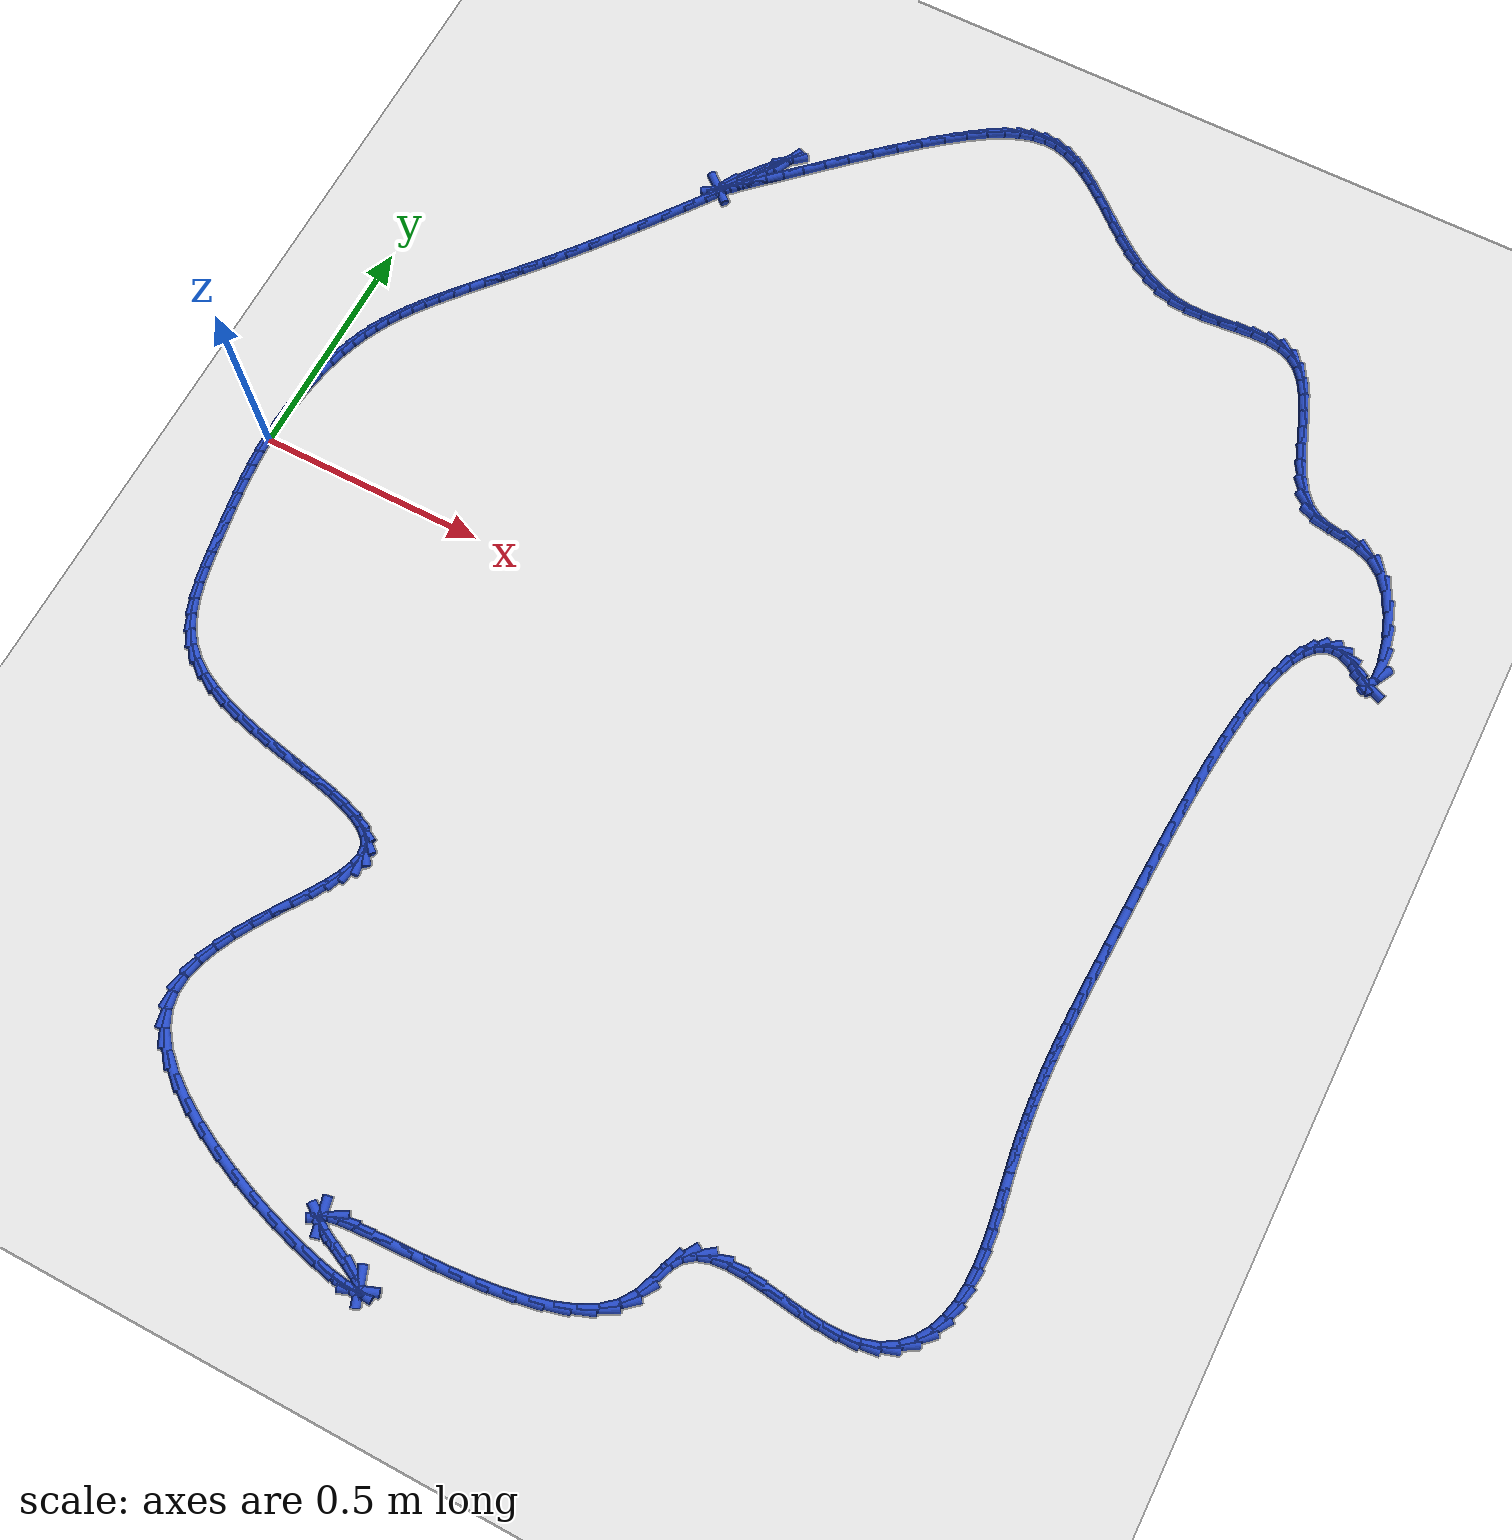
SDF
<sdf version="1.6">
 <world name="default">
  <light name="sun" type="directional">
   <pose>0 0 10 0 -0 0</pose>
   <diffuse>0.8 0.8 0.8 1</diffuse>
   <specular>0.2 0.2 0.2 1</specular>
   <attenuation>
    <range>1000</range>
    <constant>0.9</constant>
    <linear>0.01</linear>
    <quadratic>0.001</quadratic>
   </attenuation>
   <direction>-0.5 0.1 -0.9</direction>
  </light>
  <model name="ground_plane">
   <static>1</static>
   <link name="link">
    <collision name="collision">
     <geometry><plane><normal>0 0 1</normal><size>100 100</size></plane></geometry>
     <surface><friction><ode><mu>100</mu><mu2>50</mu2></ode></friction></surface>
    </collision>
    <visual name="visual">
     <cast_shadows>0</cast_shadows>
     <geometry><plane><normal>0 0 1</normal><size>100 100</size></plane></geometry>
     <material>
      <script><uri>file://media/materials/scripts/gazebo.material</uri><name>Gazebo/WhiteGlow</name></script>
     </material>
    </visual>
   </link>
  </model>
  <gravity>0 0 -9.8</gravity>
  <magnetic_field>6e-06 2.3e-05 -4.2e-05</magnetic_field>
  <atmosphere type="adiabatic"/>
  <physics name="default_physics" default="0" type="ode">
   <max_step_size>0.001</max_step_size>
   <real_time_factor>1</real_time_factor>
   <real_time_update_rate>1000</real_time_update_rate>
  </physics>
  <scene><ambient>0.4 0.4 0.4 1</ambient><background>0.7 0.7 0.7 1</background><shadows>1</shadows></scene>
  <spherical_coordinates>
   <surface_model>EARTH_WGS84</surface_model>
   <latitude_deg>0</latitude_deg>
   <longitude_deg>0</longitude_deg>
   <elevation>0</elevation>
   <heading_deg>0</heading_deg>
  </spherical_coordinates>
  <model name="line">
   <link name="link_0">
    <pose>-3.469446951953614e-18 -2.0816681711721685e-17 0.01 0 1.57 -1.5707592864873938</pose>
    <collision name="collision">
     <geometry><cylinder><radius>0.01</radius><length>0.08</length></cylinder></geometry>
    </collision>
    <visual name="visual">
     <material>
      <script><name>Gazebo/Blue</name><uri>file://media/materials/scripts/gazebo.material</uri></script>
     </material>
     <geometry><cylinder><radius>0.01</radius><length>0.08</length></cylinder></geometry>
    </visual>
   </link>
   <link name="link_1">
    <pose>-1.321990990803127e-06 0.03569060516281446 0.01 0 1.57 1.5304173241686705</pose>
    <collision name="collision">
     <geometry><cylinder><radius>0.01</radius><length>0.08</length></cylinder></geometry>
    </collision>
    <visual name="visual">
     <material>
      <script><name>Gazebo/Blue</name><uri>file://media/materials/scripts/gazebo.material</uri></script>
     </material>
     <geometry><cylinder><radius>0.01</radius><length>0.08</length></cylinder></geometry>
    </visual>
   </link>
   <link name="link_2">
    <pose>0.0014527882783550929 0.07168257617487195 0.01 0 1.57 1.4906871543346432</pose>
    <collision name="collision">
     <geometry><cylinder><radius>0.01</radius><length>0.08</length></cylinder></geometry>
    </collision>
    <visual name="visual">
     <material>
      <script><name>Gazebo/Blue</name><uri>file://media/materials/scripts/gazebo.material</uri></script>
     </material>
     <geometry><cylinder><radius>0.01</radius><length>0.08</length></cylinder></geometry>
    </visual>
   </link>
   <link name="link_3">
    <pose>0.004335432446679731 0.1075895142138233 0.01 0 1.57 1.45047673911087</pose>
    <collision name="collision">
     <geometry><cylinder><radius>0.01</radius><length>0.08</length></cylinder></geometry>
    </collision>
    <visual name="visual">
     <material>
      <script><name>Gazebo/Blue</name><uri>file://media/materials/scripts/gazebo.material</uri></script>
     </material>
     <geometry><cylinder><radius>0.01</radius><length>0.08</length></cylinder></geometry>
    </visual>
   </link>
   <link name="link_4">
    <pose>0.008619712152625157 0.14302502045731946 0.01 0 1.57 1.4085735020318906</pose>
    <collision name="collision">
     <geometry><cylinder><radius>0.01</radius><length>0.08</length></cylinder></geometry>
    </collision>
    <visual name="visual">
     <material>
      <script><name>Gazebo/Blue</name><uri>file://media/materials/scripts/gazebo.material</uri></script>
     </material>
     <geometry><cylinder><radius>0.01</radius><length>0.08</length></cylinder></geometry>
    </visual>
   </link>
   <link name="link_5">
    <pose>0.014278729034833414 0.17760269608301127 0.01 0 1.57 1.3636078383511694</pose>
    <collision name="collision">
     <geometry><cylinder><radius>0.01</radius><length>0.08</length></cylinder></geometry>
    </collision>
    <visual name="visual">
     <material>
      <script><name>Gazebo/Blue</name><uri>file://media/materials/scripts/gazebo.material</uri></script>
     </material>
     <geometry><cylinder><radius>0.01</radius><length>0.08</length></cylinder></geometry>
    </visual>
   </link>
   <link name="link_6">
    <pose>0.02128558473194655 0.21093614226854962 0.01 0 1.57 1.3139166584926567</pose>
    <collision name="collision">
     <geometry><cylinder><radius>0.01</radius><length>0.08</length></cylinder></geometry>
    </collision>
    <visual name="visual">
     <material>
      <script><name>Gazebo/Blue</name><uri>file://media/materials/scripts/gazebo.material</uri></script>
     </material>
     <geometry><cylinder><radius>0.01</radius><length>0.08</length></cylinder></geometry>
    </visual>
   </link>
   <link name="link_7">
    <pose>0.029613380882606604 0.2426389601915854 0.01 0 1.57 1.2578349997189717</pose>
    <collision name="collision">
     <geometry><cylinder><radius>0.01</radius><length>0.08</length></cylinder></geometry>
    </collision>
    <visual name="visual">
     <material>
      <script><name>Gazebo/Blue</name><uri>file://media/materials/scripts/gazebo.material</uri></script>
     </material>
     <geometry><cylinder><radius>0.01</radius><length>0.08</length></cylinder></geometry>
    </visual>
   </link>
   <link name="link_8">
    <pose>0.03924030749667579 0.27238881024362055 0.01 0 1.57 1.1976031780181058</pose>
    <collision name="collision">
     <geometry><cylinder><radius>0.01</radius><length>0.08</length></cylinder></geometry>
    </collision>
    <visual name="visual">
     <material>
      <script><name>Gazebo/Blue</name><uri>file://media/materials/scripts/gazebo.material</uri></script>
     </material>
     <geometry><cylinder><radius>0.01</radius><length>0.08</length></cylinder></geometry>
    </visual>
   </link>
   <link name="link_9">
    <pose>0.05018192319062259 0.3003337987522592 0.01 0 1.57 1.1365635758216672</pose>
    <collision name="collision">
     <geometry><cylinder><radius>0.01</radius><length>0.08</length></cylinder></geometry>
    </collision>
    <visual name="visual">
     <material>
      <script><name>Gazebo/Blue</name><uri>file://media/materials/scripts/gazebo.material</uri></script>
     </material>
     <geometry><cylinder><radius>0.01</radius><length>0.08</length></cylinder></geometry>
    </visual>
   </link>
   <link name="link_10">
    <pose>0.06247044276273264 0.32683172231077307 0.01 0 1.57 1.077294029438978</pose>
    <collision name="collision">
     <geometry><cylinder><radius>0.01</radius><length>0.08</length></cylinder></geometry>
    </collision>
    <visual name="visual">
     <material>
      <script><name>Gazebo/Blue</name><uri>file://media/materials/scripts/gazebo.material</uri></script>
     </material>
     <geometry><cylinder><radius>0.01</radius><length>0.08</length></cylinder></geometry>
    </visual>
   </link>
   <link name="link_11">
    <pose>0.07613815761532017 0.35224134190627077 0.01 0 1.57 1.0223374243256331</pose>
    <collision name="collision">
     <geometry><cylinder><radius>0.01</radius><length>0.08</length></cylinder></geometry>
    </collision>
    <visual name="visual">
     <material>
      <script><name>Gazebo/Blue</name><uri>file://media/materials/scripts/gazebo.material</uri></script>
     </material>
     <geometry><cylinder><radius>0.01</radius><length>0.08</length></cylinder></geometry>
    </visual>
   </link>
   <link name="link_12">
    <pose>0.09121735915069937 0.37692141852586053 0.01 0 1.57 0.9738261884577403</pose>
    <collision name="collision">
     <geometry><cylinder><radius>0.01</radius><length>0.08</length></cylinder></geometry>
    </collision>
    <visual name="visual">
     <material>
      <script><name>Gazebo/Blue</name><uri>file://media/materials/scripts/gazebo.material</uri></script>
     </material>
     <geometry><cylinder><radius>0.01</radius><length>0.08</length></cylinder></geometry>
    </visual>
   </link>
   <link name="link_13">
    <pose>0.1077403387711844 0.4012307131566508 0.01 0 1.57 0.9332191299139411</pose>
    <collision name="collision">
     <geometry><cylinder><radius>0.01</radius><length>0.08</length></cylinder></geometry>
    </collision>
    <visual name="visual">
     <material>
      <script><name>Gazebo/Blue</name><uri>file://media/materials/scripts/gazebo.material</uri></script>
     </material>
     <geometry><cylinder><radius>0.01</radius><length>0.08</length></cylinder></geometry>
    </visual>
   </link>
   <link name="link_14">
    <pose>0.12573938787908945 0.42552798678575016 0.01 0 1.57 0.9012181013214329</pose>
    <collision name="collision">
     <geometry><cylinder><radius>0.01</radius><length>0.08</length></cylinder></geometry>
    </collision>
    <visual name="visual">
     <material>
      <script><name>Gazebo/Blue</name><uri>file://media/materials/scripts/gazebo.material</uri></script>
     </material>
     <geometry><cylinder><radius>0.01</radius><length>0.08</length></cylinder></geometry>
    </visual>
   </link>
   <link name="link_15">
    <pose>0.14524679787672864 0.45017200040026656 0.01 0 1.57 0.8778424733503216</pose>
    <collision name="collision">
     <geometry><cylinder><radius>0.01</radius><length>0.08</length></cylinder></geometry>
    </collision>
    <visual name="visual">
     <material>
      <script><name>Gazebo/Blue</name><uri>file://media/materials/scripts/gazebo.material</uri></script>
     </material>
     <geometry><cylinder><radius>0.01</radius><length>0.08</length></cylinder></geometry>
    </visual>
   </link>
   <link name="link_16">
    <pose>0.1662948601664163 0.4755215149873088 0.01 0 1.57 0.8625930361971438</pose>
    <collision name="collision">
     <geometry><cylinder><radius>0.01</radius><length>0.08</length></cylinder></geometry>
    </collision>
    <visual name="visual">
     <material>
      <script><name>Gazebo/Blue</name><uri>file://media/materials/scripts/gazebo.material</uri></script>
     </material>
     <geometry><cylinder><radius>0.01</radius><length>0.08</length></cylinder></geometry>
    </visual>
   </link>
   <link name="link_17">
    <pose>0.18891586615046652 0.5019352915339852 0.01 0 1.57 0.8546370481776571</pose>
    <collision name="collision">
     <geometry><cylinder><radius>0.01</radius><length>0.08</length></cylinder></geometry>
    </collision>
    <visual name="visual">
     <material>
      <script><name>Gazebo/Blue</name><uri>file://media/materials/scripts/gazebo.material</uri></script>
     </material>
     <geometry><cylinder><radius>0.01</radius><length>0.08</length></cylinder></geometry>
    </visual>
   </link>
   <link name="link_18">
    <pose>0.2131421072311935 0.529772091027404 0.01 0 1.57 0.8529709879256517</pose>
    <collision name="collision">
     <geometry><cylinder><radius>0.01</radius><length>0.08</length></cylinder></geometry>
    </collision>
    <visual name="visual">
     <material>
      <script><name>Gazebo/Blue</name><uri>file://media/materials/scripts/gazebo.material</uri></script>
     </material>
     <geometry><cylinder><radius>0.01</radius><length>0.08</length></cylinder></geometry>
    </visual>
   </link>
   <link name="link_19">
    <pose>0.23900587481091135 0.5593906744546736 0.01 0 1.57 0.8565436841870587</pose>
    <collision name="collision">
     <geometry><cylinder><radius>0.01</radius><length>0.08</length></cylinder></geometry>
    </collision>
    <visual name="visual">
     <material>
      <script><name>Gazebo/Blue</name><uri>file://media/materials/scripts/gazebo.material</uri></script>
     </material>
     <geometry><cylinder><radius>0.01</radius><length>0.08</length></cylinder></geometry>
    </visual>
   </link>
   <link name="link_20">
    <pose>0.26653946029193437 0.5911498028029026 0.01 0 1.57 0.8643393472643787</pose>
    <collision name="collision">
     <geometry><cylinder><radius>0.01</radius><length>0.08</length></cylinder></geometry>
    </collision>
    <visual name="visual">
     <material>
      <script><name>Gazebo/Blue</name><uri>file://media/materials/scripts/gazebo.material</uri></script>
     </material>
     <geometry><cylinder><radius>0.01</radius><length>0.08</length></cylinder></geometry>
    </visual>
   </link>
   <link name="link_21">
    <pose>0.2957751550765767 0.6254082370591991 0.01 0 1.57 0.87542749178564</pose>
    <collision name="collision">
     <geometry><cylinder><radius>0.01</radius><length>0.08</length></cylinder></geometry>
    </collision>
    <visual name="visual">
     <material>
      <script><name>Gazebo/Blue</name><uri>file://media/materials/scripts/gazebo.material</uri></script>
     </material>
     <geometry><cylinder><radius>0.01</radius><length>0.08</length></cylinder></geometry>
    </visual>
   </link>
   <link name="link_22">
    <pose>0.3267452505671524 0.6625247382106717 0.01 0 1.57 0.8888215452859668</pose>
    <collision name="collision">
     <geometry><cylinder><radius>0.01</radius><length>0.08</length></cylinder></geometry>
    </collision>
    <visual name="visual">
     <material>
      <script><name>Gazebo/Blue</name><uri>file://media/materials/scripts/gazebo.material</uri></script>
     </material>
     <geometry><cylinder><radius>0.01</radius><length>0.08</length></cylinder></geometry>
    </visual>
   </link>
   <link name="link_23">
    <pose>0.3594605537952452 0.7028178570839259 0.01 0 1.57 0.9013056689274274</pose>
    <collision name="collision">
     <geometry><cylinder><radius>0.01</radius><length>0.08</length></cylinder></geometry>
    </collision>
    <visual name="visual">
     <material>
      <script><name>Gazebo/Blue</name><uri>file://media/materials/scripts/gazebo.material</uri></script>
     </material>
     <geometry><cylinder><radius>0.01</radius><length>0.08</length></cylinder></geometry>
    </visual>
   </link>
   <link name="link_24">
    <pose>0.39354983607669625 0.7458911262422728 0.01 0 1.57 0.9113345819190084</pose>
    <collision name="collision">
     <geometry><cylinder><radius>0.01</radius><length>0.08</length></cylinder></geometry>
    </collision>
    <visual name="visual">
     <material>
      <script><name>Gazebo/Blue</name><uri>file://media/materials/scripts/gazebo.material</uri></script>
     </material>
     <geometry><cylinder><radius>0.01</radius><length>0.08</length></cylinder></geometry>
    </visual>
   </link>
   <link name="link_25">
    <pose>0.42831335326093006 0.7907332285148665 0.01 0 1.57 0.9197195872085189</pose>
    <collision name="collision">
     <geometry><cylinder><radius>0.01</radius><length>0.08</length></cylinder></geometry>
    </collision>
    <visual name="visual">
     <material>
      <script><name>Gazebo/Blue</name><uri>file://media/materials/scripts/gazebo.material</uri></script>
     </material>
     <geometry><cylinder><radius>0.01</radius><length>0.08</length></cylinder></geometry>
    </visual>
   </link>
   <link name="link_26">
    <pose>0.463040657372221 0.8363128134456101 0.01 0 1.57 0.9270641181634669</pose>
    <collision name="collision">
     <geometry><cylinder><radius>0.01</radius><length>0.08</length></cylinder></geometry>
    </collision>
    <visual name="visual">
     <material>
      <script><name>Gazebo/Blue</name><uri>file://media/materials/scripts/gazebo.material</uri></script>
     </material>
     <geometry><cylinder><radius>0.01</radius><length>0.08</length></cylinder></geometry>
    </visual>
   </link>
   <link name="link_27">
    <pose>0.49702130043484294 0.8815985305784064 0.01 0 1.57 0.9338323528605587</pose>
    <collision name="collision">
     <geometry><cylinder><radius>0.01</radius><length>0.08</length></cylinder></geometry>
    </collision>
    <visual name="visual">
     <material>
      <script><name>Gazebo/Blue</name><uri>file://media/materials/scripts/gazebo.material</uri></script>
     </material>
     <geometry><cylinder><radius>0.01</radius><length>0.08</length></cylinder></geometry>
    </visual>
   </link>
   <link name="link_28">
    <pose>0.5295448344730707 0.9255590294571586 0.01 0 1.57 0.9404521188077047</pose>
    <collision name="collision">
     <geometry><cylinder><radius>0.01</radius><length>0.08</length></cylinder></geometry>
    </collision>
    <visual name="visual">
     <material>
      <script><name>Gazebo/Blue</name><uri>file://media/materials/scripts/gazebo.material</uri></script>
     </material>
     <geometry><cylinder><radius>0.01</radius><length>0.08</length></cylinder></geometry>
    </visual>
   </link>
   <link name="link_29">
    <pose>0.5599008115111788 0.9671629596257708 0.01 0 1.57 0.9474207868611886</pose>
    <collision name="collision">
     <geometry><cylinder><radius>0.01</radius><length>0.08</length></cylinder></geometry>
    </collision>
    <visual name="visual">
     <material>
      <script><name>Gazebo/Blue</name><uri>file://media/materials/scripts/gazebo.material</uri></script>
     </material>
     <geometry><cylinder><radius>0.01</radius><length>0.08</length></cylinder></geometry>
    </visual>
   </link>
   <link name="link_30">
    <pose>0.5873787835734411 1.0053789706281449 0.01 0 1.57 0.9554820558111933</pose>
    <collision name="collision">
     <geometry><cylinder><radius>0.01</radius><length>0.08</length></cylinder></geometry>
    </collision>
    <visual name="visual">
     <material>
      <script><name>Gazebo/Blue</name><uri>file://media/materials/scripts/gazebo.material</uri></script>
     </material>
     <geometry><cylinder><radius>0.01</radius><length>0.08</length></cylinder></geometry>
    </visual>
   </link>
   <link name="link_31">
    <pose>0.6112683026841323 1.039175712008185 0.01 0 1.57 0.9660538715062068</pose>
    <collision name="collision">
     <geometry><cylinder><radius>0.01</radius><length>0.08</length></cylinder></geometry>
    </collision>
    <visual name="visual">
     <material>
      <script><name>Gazebo/Blue</name><uri>file://media/materials/scripts/gazebo.material</uri></script>
     </material>
     <geometry><cylinder><radius>0.01</radius><length>0.08</length></cylinder></geometry>
    </visual>
   </link>
   <link name="link_32">
    <pose>0.6308589208675263 1.0675218333097936 0.01 0 1.57 0.9826300769140391</pose>
    <collision name="collision">
     <geometry><cylinder><radius>0.01</radius><length>0.08</length></cylinder></geometry>
    </collision>
    <visual name="visual">
     <material>
      <script><name>Gazebo/Blue</name><uri>file://media/materials/scripts/gazebo.material</uri></script>
     </material>
     <geometry><cylinder><radius>0.01</radius><length>0.08</length></cylinder></geometry>
    </visual>
   </link>
   <link name="link_33">
    <pose>0.6454401901478979 1.089385984076874 0.01 0 1.57 1.0176167810779266</pose>
    <collision name="collision">
     <geometry><cylinder><radius>0.01</radius><length>0.08</length></cylinder></geometry>
    </collision>
    <visual name="visual">
     <material>
      <script><name>Gazebo/Blue</name><uri>file://media/materials/scripts/gazebo.material</uri></script>
     </material>
     <geometry><cylinder><radius>0.01</radius><length>0.08</length></cylinder></geometry>
    </visual>
   </link>
   <link name="link_34">
    <pose>0.6543016625495212 1.1037368138533301 0.01 0 1.57 1.1742462103656968</pose>
    <collision name="collision">
     <geometry><cylinder><radius>0.01</radius><length>0.08</length></cylinder></geometry>
    </collision>
    <visual name="visual">
     <material>
      <script><name>Gazebo/Blue</name><uri>file://media/materials/scripts/gazebo.material</uri></script>
     </material>
     <geometry><cylinder><radius>0.01</radius><length>0.08</length></cylinder></geometry>
    </visual>
   </link>
   <link name="link_35">
    <pose>0.6567328900966707 1.1095429721830643 0.01 0 1.57 0.6750375429932046</pose>
    <collision name="collision">
     <geometry><cylinder><radius>0.01</radius><length>0.08</length></cylinder></geometry>
    </collision>
    <visual name="visual">
     <material>
      <script><name>Gazebo/Blue</name><uri>file://media/materials/scripts/gazebo.material</uri></script>
     </material>
     <geometry><cylinder><radius>0.01</radius><length>0.08</length></cylinder></geometry>
    </visual>
   </link>
   <link name="link_36">
    <pose>0.6520234248136205 1.1057731086099796 0.01 0 1.57 0.852734047417088</pose>
    <collision name="collision">
     <geometry><cylinder><radius>0.01</radius><length>0.08</length></cylinder></geometry>
    </collision>
    <visual name="visual">
     <material>
      <script><name>Gazebo/Blue</name><uri>file://media/materials/scripts/gazebo.material</uri></script>
     </material>
     <geometry><cylinder><radius>0.01</radius><length>0.08</length></cylinder></geometry>
    </visual>
   </link>
   <link name="link_37">
    <pose>0.6394628187246454 1.0913958726779802 0.01 0 1.57 0.8881695675735664</pose>
    <collision name="collision">
     <geometry><cylinder><radius>0.01</radius><length>0.08</length></cylinder></geometry>
    </collision>
    <visual name="visual">
     <material>
      <script><name>Gazebo/Blue</name><uri>file://media/materials/scripts/gazebo.material</uri></script>
     </material>
     <geometry><cylinder><radius>0.01</radius><length>0.08</length></cylinder></geometry>
    </visual>
   </link>
   <link name="link_38">
    <pose>0.6192438460404104 1.0665267500156475 0.01 0 1.57 0.9051832364251783</pose>
    <collision name="collision">
     <geometry><cylinder><radius>0.01</radius><length>0.08</length></cylinder></geometry>
    </collision>
    <visual name="visual">
     <material>
      <script><name>Gazebo/Blue</name><uri>file://media/materials/scripts/gazebo.material</uri></script>
     </material>
     <geometry><cylinder><radius>0.01</radius><length>0.08</length></cylinder></geometry>
    </visual>
   </link>
   <link name="link_39">
    <pose>0.5954180213533699 1.0361807324615757 0.01 0 1.57 0.9224087407581062</pose>
    <collision name="collision">
     <geometry><cylinder><radius>0.01</radius><length>0.08</length></cylinder></geometry>
    </collision>
    <visual name="visual">
     <material>
      <script><name>Gazebo/Blue</name><uri>file://media/materials/scripts/gazebo.material</uri></script>
     </material>
     <geometry><cylinder><radius>0.01</radius><length>0.08</length></cylinder></geometry>
    </visual>
   </link>
   <link name="link_40">
    <pose>0.573067132796172 1.0066809671352936 0.01 0 1.57 0.9550504454815214</pose>
    <collision name="collision">
     <geometry><cylinder><radius>0.01</radius><length>0.08</length></cylinder></geometry>
    </collision>
    <visual name="visual">
     <material>
      <script><name>Gazebo/Blue</name><uri>file://media/materials/scripts/gazebo.material</uri></script>
     </material>
     <geometry><cylinder><radius>0.01</radius><length>0.08</length></cylinder></geometry>
    </visual>
   </link>
   <link name="link_41">
    <pose>0.5572335288671827 0.984301508377082 0.01 0 1.57 1.0654862560269127</pose>
    <collision name="collision">
     <geometry><cylinder><radius>0.01</radius><length>0.08</length></cylinder></geometry>
    </collision>
    <visual name="visual">
     <material>
      <script><name>Gazebo/Blue</name><uri>file://media/materials/scripts/gazebo.material</uri></script>
     </material>
     <geometry><cylinder><radius>0.01</radius><length>0.08</length></cylinder></geometry>
    </visual>
   </link>
   <link name="link_42">
    <pose>0.5507219267041502 0.9725310877537243 0.01 0 1.57 -0.7080051592350588</pose>
    <collision name="collision">
     <geometry><cylinder><radius>0.01</radius><length>0.08</length></cylinder></geometry>
    </collision>
    <visual name="visual">
     <material>
      <script><name>Gazebo/Blue</name><uri>file://media/materials/scripts/gazebo.material</uri></script>
     </material>
     <geometry><cylinder><radius>0.01</radius><length>0.08</length></cylinder></geometry>
    </visual>
   </link>
   <link name="link_43">
    <pose>0.5529411190385555 0.9706313126719084 0.01 0 1.57 0.5990892341146937</pose>
    <collision name="collision">
     <geometry><cylinder><radius>0.01</radius><length>0.08</length></cylinder></geometry>
    </collision>
    <visual name="visual">
     <material>
      <script><name>Gazebo/Blue</name><uri>file://media/materials/scripts/gazebo.material</uri></script>
     </material>
     <geometry><cylinder><radius>0.01</radius><length>0.08</length></cylinder></geometry>
    </visual>
   </link>
   <link name="link_44">
    <pose>0.5630160775906404 0.9775105003851202 0.01 0 1.57 0.7068423049731728</pose>
    <collision name="collision">
     <geometry><cylinder><radius>0.01</radius><length>0.08</length></cylinder></geometry>
    </collision>
    <visual name="visual">
     <material>
      <script><name>Gazebo/Blue</name><uri>file://media/materials/scripts/gazebo.material</uri></script>
     </material>
     <geometry><cylinder><radius>0.01</radius><length>0.08</length></cylinder></geometry>
    </visual>
   </link>
   <link name="link_45">
    <pose>0.5800717740806469 0.9920769681468455 0.01 0 1.57 0.7403207665954509</pose>
    <collision name="collision">
     <geometry><cylinder><radius>0.01</radius><length>0.08</length></cylinder></geometry>
    </collision>
    <visual name="visual">
     <material>
      <script><name>Gazebo/Blue</name><uri>file://media/materials/scripts/gazebo.material</uri></script>
     </material>
     <geometry><cylinder><radius>0.01</radius><length>0.08</length></cylinder></geometry>
    </visual>
   </link>
   <link name="link_46">
    <pose>0.6032331802288169 1.0132390332105705 0.01 0 1.57 0.7540577473674985</pose>
    <collision name="collision">
     <geometry><cylinder><radius>0.01</radius><length>0.08</length></cylinder></geometry>
    </collision>
    <visual name="visual">
     <material>
      <script><name>Gazebo/Blue</name><uri>file://media/materials/scripts/gazebo.material</uri></script>
     </material>
     <geometry><cylinder><radius>0.01</radius><length>0.08</length></cylinder></geometry>
    </visual>
   </link>
   <link name="link_47">
    <pose>0.6316252677553921 1.039905012829781 0.01 0 1.57 0.7592465976700655</pose>
    <collision name="collision">
     <geometry><cylinder><radius>0.01</radius><length>0.08</length></cylinder></geometry>
    </collision>
    <visual name="visual">
     <material>
      <script><name>Gazebo/Blue</name><uri>file://media/materials/scripts/gazebo.material</uri></script>
     </material>
     <geometry><cylinder><radius>0.01</radius><length>0.08</length></cylinder></geometry>
    </visual>
   </link>
   <link name="link_48">
    <pose>0.6643730083806143 1.0709832242579629 0.01 0 1.57 0.7594988247779761</pose>
    <collision name="collision">
     <geometry><cylinder><radius>0.01</radius><length>0.08</length></cylinder></geometry>
    </collision>
    <visual name="visual">
     <material>
      <script><name>Gazebo/Blue</name><uri>file://media/materials/scripts/gazebo.material</uri></script>
     </material>
     <geometry><cylinder><radius>0.01</radius><length>0.08</length></cylinder></geometry>
    </visual>
   </link>
   <link name="link_49">
    <pose>0.7006013738247251 1.105381984748602 0.01 0 1.57 0.756168633017891</pose>
    <collision name="collision">
     <geometry><cylinder><radius>0.01</radius><length>0.08</length></cylinder></geometry>
    </collision>
    <visual name="visual">
     <material>
      <script><name>Gazebo/Blue</name><uri>file://media/materials/scripts/gazebo.material</uri></script>
     </material>
     <geometry><cylinder><radius>0.01</radius><length>0.08</length></cylinder></geometry>
    </visual>
   </link>
   <link name="link_50">
    <pose>0.7394353358079666 1.142009611555184 0.01 0 1.57 0.7496704464202273</pose>
    <collision name="collision">
     <geometry><cylinder><radius>0.01</radius><length>0.08</length></cylinder></geometry>
    </collision>
    <visual name="visual">
     <material>
      <script><name>Gazebo/Blue</name><uri>file://media/materials/scripts/gazebo.material</uri></script>
     </material>
     <geometry><cylinder><radius>0.01</radius><length>0.08</length></cylinder></geometry>
    </visual>
   </link>
   <link name="link_51">
    <pose>0.7799998660505805 1.1797744219311954 0.01 0 1.57 0.7398693596176621</pose>
    <collision name="collision">
     <geometry><cylinder><radius>0.01</radius><length>0.08</length></cylinder></geometry>
    </collision>
    <visual name="visual">
     <material>
      <script><name>Gazebo/Blue</name><uri>file://media/materials/scripts/gazebo.material</uri></script>
     </material>
     <geometry><cylinder><radius>0.01</radius><length>0.08</length></cylinder></geometry>
    </visual>
   </link>
   <link name="link_52">
    <pose>0.8214199362728086 1.2175847331301215 0.01 0 1.57 0.7261511408955652</pose>
    <collision name="collision">
     <geometry><cylinder><radius>0.01</radius><length>0.08</length></cylinder></geometry>
    </collision>
    <visual name="visual">
     <material>
      <script><name>Gazebo/Blue</name><uri>file://media/materials/scripts/gazebo.material</uri></script>
     </material>
     <geometry><cylinder><radius>0.01</radius><length>0.08</length></cylinder></geometry>
    </visual>
   </link>
   <link name="link_53">
    <pose>0.8628205181948926 1.2543488624054484 0.01 0 1.57 0.7072980828887583</pose>
    <collision name="collision">
     <geometry><cylinder><radius>0.01</radius><length>0.08</length></cylinder></geometry>
    </collision>
    <visual name="visual">
     <material>
      <script><name>Gazebo/Blue</name><uri>file://media/materials/scripts/gazebo.material</uri></script>
     </material>
     <geometry><cylinder><radius>0.01</radius><length>0.08</length></cylinder></geometry>
    </visual>
   </link>
   <link name="link_54">
    <pose>0.9033265835370745 1.2889751270106624 0.01 0 1.57 0.6811182097032304</pose>
    <collision name="collision">
     <geometry><cylinder><radius>0.01</radius><length>0.08</length></cylinder></geometry>
    </collision>
    <visual name="visual">
     <material>
      <script><name>Gazebo/Blue</name><uri>file://media/materials/scripts/gazebo.material</uri></script>
     </material>
     <geometry><cylinder><radius>0.01</radius><length>0.08</length></cylinder></geometry>
    </visual>
   </link>
   <link name="link_55">
    <pose>0.942067848069886 1.320375405946647 0.01 0 1.57 0.6436211108280099</pose>
    <collision name="collision">
     <geometry><cylinder><radius>0.01</radius><length>0.08</length></cylinder></geometry>
    </collision>
    <visual name="visual">
     <material>
      <script><name>Gazebo/Blue</name><uri>file://media/materials/scripts/gazebo.material</uri></script>
     </material>
     <geometry><cylinder><radius>0.01</radius><length>0.08</length></cylinder></geometry>
    </visual>
   </link>
   <link name="link_56">
    <pose>0.9785659658392218 1.3477558384027826 0.01 0 1.57 0.5901309701207232</pose>
    <collision name="collision">
     <geometry><cylinder><radius>0.01</radius><length>0.08</length></cylinder></geometry>
    </collision>
    <visual name="visual">
     <material>
      <script><name>Gazebo/Blue</name><uri>file://media/materials/scripts/gazebo.material</uri></script>
     </material>
     <geometry><cylinder><radius>0.01</radius><length>0.08</length></cylinder></geometry>
    </visual>
   </link>
   <link name="link_57">
    <pose>1.0130214481804625 1.3708322373781336 0.01 0 1.57 0.516005729338417</pose>
    <collision name="collision">
     <geometry><cylinder><radius>0.01</radius><length>0.08</length></cylinder></geometry>
    </collision>
    <visual name="visual">
     <material>
      <script><name>Gazebo/Blue</name><uri>file://media/materials/scripts/gazebo.material</uri></script>
     </material>
     <geometry><cylinder><radius>0.01</radius><length>0.08</length></cylinder></geometry>
    </visual>
   </link>
   <link name="link_58">
    <pose>1.04570241990977 1.389371178853719 0.01 0 1.57 0.4158831471761494</pose>
    <collision name="collision">
     <geometry><cylinder><radius>0.01</radius><length>0.08</length></cylinder></geometry>
    </collision>
    <visual name="visual">
     <material>
      <script><name>Gazebo/Blue</name><uri>file://media/materials/scripts/gazebo.material</uri></script>
     </material>
     <geometry><cylinder><radius>0.01</radius><length>0.08</length></cylinder></geometry>
    </visual>
   </link>
   <link name="link_59">
    <pose>1.0768770058433084 1.4031392388105606 0.01 0 1.57 0.2847889965357436</pose>
    <collision name="collision">
     <geometry><cylinder><radius>0.01</radius><length>0.08</length></cylinder></geometry>
    </collision>
    <visual name="visual">
     <material>
      <script><name>Gazebo/Blue</name><uri>file://media/materials/scripts/gazebo.material</uri></script>
     </material>
     <geometry><cylinder><radius>0.01</radius><length>0.08</length></cylinder></geometry>
    </visual>
   </link>
   <link name="link_60">
    <pose>1.1068133307972405 1.4119029932296776 0.01 0 1.57 0.12113302033196666</pose>
    <collision name="collision">
     <geometry><cylinder><radius>0.01</radius><length>0.08</length></cylinder></geometry>
    </collision>
    <visual name="visual">
     <material>
      <script><name>Gazebo/Blue</name><uri>file://media/materials/scripts/gazebo.material</uri></script>
     </material>
     <geometry><cylinder><radius>0.01</radius><length>0.08</length></cylinder></geometry>
    </visual>
   </link>
   <link name="link_61">
    <pose>1.1357795195877296 1.4154290180920903 0.01 0 1.57 -0.0687112376503828</pose>
    <collision name="collision">
     <geometry><cylinder><radius>0.01</radius><length>0.08</length></cylinder></geometry>
    </collision>
    <visual name="visual">
     <material>
      <script><name>Gazebo/Blue</name><uri>file://media/materials/scripts/gazebo.material</uri></script>
     </material>
     <geometry><cylinder><radius>0.01</radius><length>0.08</length></cylinder></geometry>
    </visual>
   </link>
   <link name="link_62">
    <pose>1.1640436970309391 1.4134838893788197 0.01 0 1.57 -0.2630722630723486</pose>
    <collision name="collision">
     <geometry><cylinder><radius>0.01</radius><length>0.08</length></cylinder></geometry>
    </collision>
    <visual name="visual">
     <material>
      <script><name>Gazebo/Blue</name><uri>file://media/materials/scripts/gazebo.material</uri></script>
     </material>
     <geometry><cylinder><radius>0.01</radius><length>0.08</length></cylinder></geometry>
    </visual>
   </link>
   <link name="link_63">
    <pose>1.1918568202912345 1.405993428063927 0.01 0 1.57 -0.423040959716247</pose>
    <collision name="collision">
     <geometry><cylinder><radius>0.01</radius><length>0.08</length></cylinder></geometry>
    </collision>
    <visual name="visual">
     <material>
      <script><name>Gazebo/Blue</name><uri>file://media/materials/scripts/gazebo.material</uri></script>
     </material>
     <geometry><cylinder><radius>0.01</radius><length>0.08</length></cylinder></geometry>
    </visual>
   </link>
   <link name="link_64">
    <pose>1.2193930363021441 1.3935959372255833 0.01 0 1.57 -0.5409516922680203</pose>
    <collision name="collision">
     <geometry><cylinder><radius>0.01</radius><length>0.08</length></cylinder></geometry>
    </collision>
    <visual name="visual">
     <material>
      <script><name>Gazebo/Blue</name><uri>file://media/materials/scripts/gazebo.material</uri></script>
     </material>
     <geometry><cylinder><radius>0.01</radius><length>0.08</length></cylinder></geometry>
    </visual>
   </link>
   <link name="link_65">
    <pose>1.246805018975649 1.3771289010068557 0.01 0 1.57 -0.6226292388037207</pose>
    <collision name="collision">
     <geometry><cylinder><radius>0.01</radius><length>0.08</length></cylinder></geometry>
    </collision>
    <visual name="visual">
     <material>
      <script><name>Gazebo/Blue</name><uri>file://media/materials/scripts/gazebo.material</uri></script>
     </material>
     <geometry><cylinder><radius>0.01</radius><length>0.08</length></cylinder></geometry>
    </visual>
   </link>
   <link name="link_66">
    <pose>1.2742454412244615 1.3574298128199085 0.01 0 1.57 -0.6746618842336378</pose>
    <collision name="collision">
     <geometry><cylinder><radius>0.01</radius><length>0.08</length></cylinder></geometry>
    </collision>
    <visual name="visual">
     <material>
      <script><name>Gazebo/Blue</name><uri>file://media/materials/scripts/gazebo.material</uri></script>
     </material>
     <geometry><cylinder><radius>0.01</radius><length>0.08</length></cylinder></geometry>
    </visual>
   </link>
   <link name="link_67">
    <pose>1.3018669759612935 1.335336166076906 0.01 0 1.57 -0.7021779244512198</pose>
    <collision name="collision">
     <geometry><cylinder><radius>0.01</radius><length>0.08</length></cylinder></geometry>
    </collision>
    <visual name="visual">
     <material>
      <script><name>Gazebo/Blue</name><uri>file://media/materials/scripts/gazebo.material</uri></script>
     </material>
     <geometry><cylinder><radius>0.01</radius><length>0.08</length></cylinder></geometry>
    </visual>
   </link>
   <link name="link_68">
    <pose>1.3298222960988573 1.3116854541900127 0.01 0 1.57 -0.7084563243424707</pose>
    <collision name="collision">
     <geometry><cylinder><radius>0.01</radius><length>0.08</length></cylinder></geometry>
    </collision>
    <visual name="visual">
     <material>
      <script><name>Gazebo/Blue</name><uri>file://media/materials/scripts/gazebo.material</uri></script>
     </material>
     <geometry><cylinder><radius>0.01</radius><length>0.08</length></cylinder></geometry>
    </visual>
   </link>
   <link name="link_69">
    <pose>1.3582640745498646 1.2873151705713926 0.01 0 1.57 -0.6951089414579255</pose>
    <collision name="collision">
     <geometry><cylinder><radius>0.01</radius><length>0.08</length></cylinder></geometry>
    </collision>
    <visual name="visual">
     <material>
      <script><name>Gazebo/Blue</name><uri>file://media/materials/scripts/gazebo.material</uri></script>
     </material>
     <geometry><cylinder><radius>0.01</radius><length>0.08</length></cylinder></geometry>
    </visual>
   </link>
   <link name="link_70">
    <pose>1.3873449842270282 1.2630628086332099 0.01 0 1.57 -0.6623478260778334</pose>
    <collision name="collision">
     <geometry><cylinder><radius>0.01</radius><length>0.08</length></cylinder></geometry>
    </collision>
    <visual name="visual">
     <material>
      <script><name>Gazebo/Blue</name><uri>file://media/materials/scripts/gazebo.material</uri></script>
     </material>
     <geometry><cylinder><radius>0.01</radius><length>0.08</length></cylinder></geometry>
    </visual>
   </link>
   <link name="link_71">
    <pose>1.4172176980430593 1.239765861787629 0.01 0 1.57 -0.6092436188373467</pose>
    <collision name="collision">
     <geometry><cylinder><radius>0.01</radius><length>0.08</length></cylinder></geometry>
    </collision>
    <visual name="visual">
     <material>
      <script><name>Gazebo/Blue</name><uri>file://media/materials/scripts/gazebo.material</uri></script>
     </material>
     <geometry><cylinder><radius>0.01</radius><length>0.08</length></cylinder></geometry>
    </visual>
   </link>
   <link name="link_72">
    <pose>1.4480348889106707 1.2182618234468148 0.01 0 1.57 -0.534060255051369</pose>
    <collision name="collision">
     <geometry><cylinder><radius>0.01</radius><length>0.08</length></cylinder></geometry>
    </collision>
    <visual name="visual">
     <material>
      <script><name>Gazebo/Blue</name><uri>file://media/materials/scripts/gazebo.material</uri></script>
     </material>
     <geometry><cylinder><radius>0.01</radius><length>0.08</length></cylinder></geometry>
    </visual>
   </link>
   <link name="link_73">
    <pose>1.4799492297425731 1.1993881870229313 0.01 0 1.57 -0.43487096651185925</pose>
    <collision name="collision">
     <geometry><cylinder><radius>0.01</radius><length>0.08</length></cylinder></geometry>
    </collision>
    <visual name="visual">
     <material>
      <script><name>Gazebo/Blue</name><uri>file://media/materials/scripts/gazebo.material</uri></script>
     </material>
     <geometry><cylinder><radius>0.01</radius><length>0.08</length></cylinder></geometry>
    </visual>
   </link>
   <link name="link_74">
    <pose>1.5131133934514804 1.1839824459281425 0.01 0 1.57 -0.31072662127793815</pose>
    <collision name="collision">
     <geometry><cylinder><radius>0.01</radius><length>0.08</length></cylinder></geometry>
    </collision>
    <visual name="visual">
     <material>
      <script><name>Gazebo/Blue</name><uri>file://media/materials/scripts/gazebo.material</uri></script>
     </material>
     <geometry><cylinder><radius>0.01</radius><length>0.08</length></cylinder></geometry>
    </visual>
   </link>
   <link name="link_75">
    <pose>1.547680052950104 1.1728820935746134 0.01 0 1.57 -0.1639800397209921</pose>
    <collision name="collision">
     <geometry><cylinder><radius>0.01</radius><length>0.08</length></cylinder></geometry>
    </collision>
    <visual name="visual">
     <material>
      <script><name>Gazebo/Blue</name><uri>file://media/materials/scripts/gazebo.material</uri></script>
     </material>
     <geometry><cylinder><radius>0.01</radius><length>0.08</length></cylinder></geometry>
    </visual>
   </link>
   <link name="link_76">
    <pose>1.5837952432176416 1.166906264718902 0.01 0 1.57 -0.028313933177503966</pose>
    <collision name="collision">
     <geometry><cylinder><radius>0.01</radius><length>0.08</length></cylinder></geometry>
    </collision>
    <visual name="visual">
     <material>
      <script><name>Gazebo/Blue</name><uri>file://media/materials/scripts/gazebo.material</uri></script>
     </material>
     <geometry><cylinder><radius>0.01</radius><length>0.08</length></cylinder></geometry>
    </visual>
   </link>
   <link name="link_77">
    <pose>1.621233258503906 1.1658459639004104 0.01 0 1.57 0.05507332028136856</pose>
    <collision name="collision">
     <geometry><cylinder><radius>0.01</radius><length>0.08</length></cylinder></geometry>
    </collision>
    <visual name="visual">
     <material>
      <script><name>Gazebo/Blue</name><uri>file://media/materials/scripts/gazebo.material</uri></script>
     </material>
     <geometry><cylinder><radius>0.01</radius><length>0.08</length></cylinder></geometry>
    </visual>
   </link>
   <link name="link_78">
    <pose>1.6592069558794407 1.167939418458166 0.01 0 1.57 0.08885550832855044</pose>
    <collision name="collision">
     <geometry><cylinder><radius>0.01</radius><length>0.08</length></cylinder></geometry>
    </collision>
    <visual name="visual">
     <material>
      <script><name>Gazebo/Blue</name><uri>file://media/materials/scripts/gazebo.material</uri></script>
     </material>
     <geometry><cylinder><radius>0.01</radius><length>0.08</length></cylinder></geometry>
    </visual>
   </link>
   <link name="link_79">
    <pose>1.6968825816899873 1.17129594358672 0.01 0 1.57 0.0745367281255707</pose>
    <collision name="collision">
     <geometry><cylinder><radius>0.01</radius><length>0.08</length></cylinder></geometry>
    </collision>
    <visual name="visual">
     <material>
      <script><name>Gazebo/Blue</name><uri>file://media/materials/scripts/gazebo.material</uri></script>
     </material>
     <geometry><cylinder><radius>0.01</radius><length>0.08</length></cylinder></geometry>
    </visual>
   </link>
   <link name="link_80">
    <pose>1.7334263822812863 1.174024854480624 0.01 0 1.57 0.00609080626226796</pose>
    <collision name="collision">
     <geometry><cylinder><radius>0.01</radius><length>0.08</length></cylinder></geometry>
    </collision>
    <visual name="visual">
     <material>
      <script><name>Gazebo/Blue</name><uri>file://media/materials/scripts/gazebo.material</uri></script>
     </material>
     <geometry><cylinder><radius>0.01</radius><length>0.08</length></cylinder></geometry>
    </visual>
   </link>
   <link name="link_81">
    <pose>1.7680046039990778 1.1742354663344279 0.01 0 1.57 -0.13135132176207368</pose>
    <collision name="collision">
     <geometry><cylinder><radius>0.01</radius><length>0.08</length></cylinder></geometry>
    </collision>
    <visual name="visual">
     <material>
      <script><name>Gazebo/Blue</name><uri>file://media/materials/scripts/gazebo.material</uri></script>
     </material>
     <geometry><cylinder><radius>0.01</radius><length>0.08</length></cylinder></geometry>
    </visual>
   </link>
   <link name="link_82">
    <pose>1.7997834931891037 1.170037094342684 0.01 0 1.57 -0.35700536812928224</pose>
    <collision name="collision">
     <geometry><cylinder><radius>0.01</radius><length>0.08</length></cylinder></geometry>
    </collision>
    <visual name="visual">
     <material>
      <script><name>Gazebo/Blue</name><uri>file://media/materials/scripts/gazebo.material</uri></script>
     </material>
     <geometry><cylinder><radius>0.01</radius><length>0.08</length></cylinder></geometry>
    </visual>
   </link>
   <link name="link_83">
    <pose>1.8279292961971039 1.159539053699943 0.01 0 1.57 -0.6544645578361081</pose>
    <collision name="collision">
     <geometry><cylinder><radius>0.01</radius><length>0.08</length></cylinder></geometry>
    </collision>
    <visual name="visual">
     <material>
      <script><name>Gazebo/Blue</name><uri>file://media/materials/scripts/gazebo.material</uri></script>
     </material>
     <geometry><cylinder><radius>0.01</radius><length>0.08</length></cylinder></geometry>
    </visual>
   </link>
   <link name="link_84">
    <pose>1.8517938920310761 1.1412283910152847 0.01 0 1.57 -0.9021077104812166</pose>
    <collision name="collision">
     <geometry><cylinder><radius>0.01</radius><length>0.08</length></cylinder></geometry>
    </collision>
    <visual name="visual">
     <material>
      <script><name>Gazebo/Blue</name><uri>file://media/materials/scripts/gazebo.material</uri></script>
     </material>
     <geometry><cylinder><radius>0.01</radius><length>0.08</length></cylinder></geometry>
    </visual>
   </link>
   <link name="link_85">
    <pose>1.8718415023141106 1.1158555840436455 0.01 0 1.57 -1.064414160382714</pose>
    <collision name="collision">
     <geometry><cylinder><radius>0.01</radius><length>0.08</length></cylinder></geometry>
    </collision>
    <visual name="visual">
     <material>
      <script><name>Gazebo/Blue</name><uri>file://media/materials/scripts/gazebo.material</uri></script>
     </material>
     <geometry><cylinder><radius>0.01</radius><length>0.08</length></cylinder></geometry>
    </visual>
   </link>
   <link name="link_86">
    <pose>1.8889488108343069 1.085010402047899 0.01 0 1.57 -1.1619792918980352</pose>
    <collision name="collision">
     <geometry><cylinder><radius>0.01</radius><length>0.08</length></cylinder></geometry>
    </collision>
    <visual name="visual">
     <material>
      <script><name>Gazebo/Blue</name><uri>file://media/materials/scripts/gazebo.material</uri></script>
     </material>
     <geometry><cylinder><radius>0.01</radius><length>0.08</length></cylinder></geometry>
    </visual>
   </link>
   <link name="link_87">
    <pose>1.9039931776739614 1.050283990436478 0.01 0 1.57 -1.2125563082615824</pose>
    <collision name="collision">
     <geometry><cylinder><radius>0.01</radius><length>0.08</length></cylinder></geometry>
    </collision>
    <visual name="visual">
     <material>
      <script><name>Gazebo/Blue</name><uri>file://media/materials/scripts/gazebo.material</uri></script>
     </material>
     <geometry><cylinder><radius>0.01</radius><length>0.08</length></cylinder></geometry>
    </visual>
   </link>
   <link name="link_88">
    <pose>1.9178519629153687 1.0132674946178177 0.01 0 1.57 -1.2258744730973856</pose>
    <collision name="collision">
     <geometry><cylinder><radius>0.01</radius><length>0.08</length></cylinder></geometry>
    </collision>
    <visual name="visual">
     <material>
      <script><name>Gazebo/Blue</name><uri>file://media/materials/scripts/gazebo.material</uri></script>
     </material>
     <geometry><cylinder><radius>0.01</radius><length>0.08</length></cylinder></geometry>
    </visual>
   </link>
   <link name="link_89">
    <pose>1.9314025266408268 0.97555206000035 0.01 0 1.57 -1.204641989730536</pose>
    <collision name="collision">
     <geometry><cylinder><radius>0.01</radius><length>0.08</length></cylinder></geometry>
    </collision>
    <visual name="visual">
     <material>
      <script><name>Gazebo/Blue</name><uri>file://media/materials/scripts/gazebo.material</uri></script>
     </material>
     <geometry><cylinder><radius>0.01</radius><length>0.08</length></cylinder></geometry>
    </visual>
   </link>
   <link name="link_90">
    <pose>1.945522228932631 0.9387288319925094 0.01 0 1.57 -1.1452030760626033</pose>
    <collision name="collision">
     <geometry><cylinder><radius>0.01</radius><length>0.08</length></cylinder></geometry>
    </collision>
    <visual name="visual">
     <material>
      <script><name>Gazebo/Blue</name><uri>file://media/materials/scripts/gazebo.material</uri></script>
     </material>
     <geometry><cylinder><radius>0.01</radius><length>0.08</length></cylinder></geometry>
    </visual>
   </link>
   <link name="link_91">
    <pose>1.9610884298730782 0.9043889560027298 0.01 0 1.57 -1.0369418861402935</pose>
    <collision name="collision">
     <geometry><cylinder><radius>0.01</radius><length>0.08</length></cylinder></geometry>
    </collision>
    <visual name="visual">
     <material>
      <script><name>Gazebo/Blue</name><uri>file://media/materials/scripts/gazebo.material</uri></script>
     </material>
     <geometry><cylinder><radius>0.01</radius><length>0.08</length></cylinder></geometry>
    </visual>
   </link>
   <link name="link_92">
    <pose>1.9789784895444642 0.8741235774394449 0.01 0 1.57 -0.8620343706873654</pose>
    <collision name="collision">
     <geometry><cylinder><radius>0.01</radius><length>0.08</length></cylinder></geometry>
    </collision>
    <visual name="visual">
     <material>
      <script><name>Gazebo/Blue</name><uri>file://media/materials/scripts/gazebo.material</uri></script>
     </material>
     <geometry><cylinder><radius>0.01</radius><length>0.08</length></cylinder></geometry>
    </visual>
   </link>
   <link name="link_93">
    <pose>2.0000697680290855 0.8495238417110883 0.01 0 1.57 -0.6033298712115167</pose>
    <collision name="collision">
     <geometry><cylinder><radius>0.01</radius><length>0.08</length></cylinder></geometry>
    </collision>
    <visual name="visual">
     <material>
      <script><name>Gazebo/Blue</name><uri>file://media/materials/scripts/gazebo.material</uri></script>
     </material>
     <geometry><cylinder><radius>0.01</radius><length>0.08</length></cylinder></geometry>
    </visual>
   </link>
   <link name="link_94">
    <pose>2.0252396254092386 0.8321808942260938 0.01 0 1.57 -0.3089877488273102</pose>
    <collision name="collision">
     <geometry><cylinder><radius>0.01</radius><length>0.08</length></cylinder></geometry>
    </collision>
    <visual name="visual">
     <material>
      <script><name>Gazebo/Blue</name><uri>file://media/materials/scripts/gazebo.material</uri></script>
     </material>
     <geometry><cylinder><radius>0.01</radius><length>0.08</length></cylinder></geometry>
    </visual>
   </link>
   <link name="link_95">
    <pose>2.054968277249145 0.8226911592914163 0.01 0 1.57 -0.16419532964797048</pose>
    <collision name="collision">
     <geometry><cylinder><radius>0.01</radius><length>0.08</length></cylinder></geometry>
    </collision>
    <visual name="visual">
     <material>
      <script><name>Gazebo/Blue</name><uri>file://media/materials/scripts/gazebo.material</uri></script>
     </material>
     <geometry><cylinder><radius>0.01</radius><length>0.08</length></cylinder></geometry>
    </visual>
   </link>
   <link name="link_96">
    <pose>2.087968224767038 0.8172234972383957 0.01 0 1.57 -0.18649290256003379</pose>
    <collision name="collision">
     <geometry><cylinder><radius>0.01</radius><length>0.08</length></cylinder></geometry>
    </collision>
    <visual name="visual">
     <material>
      <script><name>Gazebo/Blue</name><uri>file://media/materials/scripts/gazebo.material</uri></script>
     </material>
     <geometry><cylinder><radius>0.01</radius><length>0.08</length></cylinder></geometry>
    </visual>
   </link>
   <link name="link_97">
    <pose>2.1224603190014153 0.8107153405778412 0.01 0 1.57 -0.3532323385182785</pose>
    <collision name="collision">
     <geometry><cylinder><radius>0.01</radius><length>0.08</length></cylinder></geometry>
    </collision>
    <visual name="visual">
     <material>
      <script><name>Gazebo/Blue</name><uri>file://media/materials/scripts/gazebo.material</uri></script>
     </material>
     <geometry><cylinder><radius>0.01</radius><length>0.08</length></cylinder></geometry>
    </visual>
   </link>
   <link name="link_98">
    <pose>2.1566653910315683 0.7981040718290728 0.01 0 1.57 -0.6369542403131211</pose>
    <collision name="collision">
     <geometry><cylinder><radius>0.01</radius><length>0.08</length></cylinder></geometry>
    </collision>
    <visual name="visual">
     <material>
      <script><name>Gazebo/Blue</name><uri>file://media/materials/scripts/gazebo.material</uri></script>
     </material>
     <geometry><cylinder><radius>0.01</radius><length>0.08</length></cylinder></geometry>
    </visual>
   </link>
   <link name="link_99">
    <pose>2.1888042719367853 0.7743270735114104 0.01 0 1.57 -0.9363026649190562</pose>
    <collision name="collision">
     <geometry><cylinder><radius>0.01</radius><length>0.08</length></cylinder></geometry>
    </collision>
    <visual name="visual">
     <material>
      <script><name>Gazebo/Blue</name><uri>file://media/materials/scripts/gazebo.material</uri></script>
     </material>
     <geometry><cylinder><radius>0.01</radius><length>0.08</length></cylinder></geometry>
    </visual>
   </link>
   <link name="link_100">
    <pose>2.2171648789369764 0.7357946834804234 0.01 0 1.57 -1.1264641274387024</pose>
    <collision name="collision">
     <geometry><cylinder><radius>0.01</radius><length>0.08</length></cylinder></geometry>
    </collision>
    <visual name="visual">
     <material>
      <script><name>Gazebo/Blue</name><uri>file://media/materials/scripts/gazebo.material</uri></script>
     </material>
     <geometry><cylinder><radius>0.01</radius><length>0.08</length></cylinder></geometry>
    </visual>
   </link>
   <link name="link_101">
    <pose>2.240402559902176 0.6869846128494241 0.01 0 1.57 -1.255866447374387</pose>
    <collision name="collision">
     <geometry><cylinder><radius>0.01</radius><length>0.08</length></cylinder></geometry>
    </collision>
    <visual name="visual">
     <material>
      <script><name>Gazebo/Blue</name><uri>file://media/materials/scripts/gazebo.material</uri></script>
     </material>
     <geometry><cylinder><radius>0.01</radius><length>0.08</length></cylinder></geometry>
    </visual>
   </link>
   <link name="link_102">
    <pose>2.2572978128848513 0.6351223925845828 0.01 0 1.57 -1.3775150531442284</pose>
    <collision name="collision">
     <geometry><cylinder><radius>0.01</radius><length>0.08</length></cylinder></geometry>
    </collision>
    <visual name="visual">
     <material>
      <script><name>Gazebo/Blue</name><uri>file://media/materials/scripts/gazebo.material</uri></script>
     </material>
     <geometry><cylinder><radius>0.01</radius><length>0.08</length></cylinder></geometry>
    </visual>
   </link>
   <link name="link_103">
    <pose>2.2666312411974037 0.5874358647580553 0.01 0 1.57 -1.555578058561656</pose>
    <collision name="collision">
     <geometry><cylinder><radius>0.01</radius><length>0.08</length></cylinder></geometry>
    </collision>
    <visual name="visual">
     <material>
      <script><name>Gazebo/Blue</name><uri>file://media/materials/scripts/gazebo.material</uri></script>
     </material>
     <geometry><cylinder><radius>0.01</radius><length>0.08</length></cylinder></geometry>
    </visual>
   </link>
   <link name="link_104">
    <pose>2.2671834481522337 0.5511528714419979 0.01 0 1.57 1.07933109779361</pose>
    <collision name="collision">
     <geometry><cylinder><radius>0.01</radius><length>0.08</length></cylinder></geometry>
    </collision>
    <visual name="visual">
     <material>
      <script><name>Gazebo/Blue</name><uri>file://media/materials/scripts/gazebo.material</uri></script>
     </material>
     <geometry><cylinder><radius>0.01</radius><length>0.08</length></cylinder></geometry>
    </visual>
   </link>
   <link name="link_105">
    <pose>2.2577350370617433 0.5335012547085666 0.01 0 1.57 -0.3769102465045212</pose>
    <collision name="collision">
     <geometry><cylinder><radius>0.01</radius><length>0.08</length></cylinder></geometry>
    </collision>
    <visual name="visual">
     <material>
      <script><name>Gazebo/Blue</name><uri>file://media/materials/scripts/gazebo.material</uri></script>
     </material>
     <geometry><cylinder><radius>0.01</radius><length>0.08</length></cylinder></geometry>
    </visual>
   </link>
   <link name="link_106">
    <pose>2.237076962986386 0.5416784323557527 0.01 0 1.57 -0.656801739641008</pose>
    <collision name="collision">
     <geometry><cylinder><radius>0.01</radius><length>0.08</length></cylinder></geometry>
    </collision>
    <visual name="visual">
     <material>
      <script><name>Gazebo/Blue</name><uri>file://media/materials/scripts/gazebo.material</uri></script>
     </material>
     <geometry><cylinder><radius>0.01</radius><length>0.08</length></cylinder></geometry>
    </visual>
   </link>
   <link name="link_107">
    <pose>2.21109851242775 0.5617076329680778 0.01 0 1.57 -0.4300035500214459</pose>
    <collision name="collision">
     <geometry><cylinder><radius>0.01</radius><length>0.08</length></cylinder></geometry>
    </collision>
    <visual name="visual">
     <material>
      <script><name>Gazebo/Blue</name><uri>file://media/materials/scripts/gazebo.material</uri></script>
     </material>
     <geometry><cylinder><radius>0.01</radius><length>0.08</length></cylinder></geometry>
    </visual>
   </link>
   <link name="link_108">
    <pose>2.1873478235861645 0.5726003002430565 0.01 0 1.57 -0.10359915343444842</pose>
    <collision name="collision">
     <geometry><cylinder><radius>0.01</radius><length>0.08</length></cylinder></geometry>
    </collision>
    <visual name="visual">
     <material>
      <script><name>Gazebo/Blue</name><uri>file://media/materials/scripts/gazebo.material</uri></script>
     </material>
     <geometry><cylinder><radius>0.01</radius><length>0.08</length></cylinder></geometry>
    </visual>
   </link>
   <link name="link_109">
    <pose>2.1657609835300864 0.5748447139523627 0.01 0 1.57 0.28761097088837906</pose>
    <collision name="collision">
     <geometry><cylinder><radius>0.01</radius><length>0.08</length></cylinder></geometry>
    </collision>
    <visual name="visual">
     <material>
      <script><name>Gazebo/Blue</name><uri>file://media/materials/scripts/gazebo.material</uri></script>
     </material>
     <geometry><cylinder><radius>0.01</radius><length>0.08</length></cylinder></geometry>
    </visual>
   </link>
   <link name="link_110">
    <pose>2.1462264318307858 0.5690661422957188 0.01 0 1.57 0.6428067218936064</pose>
    <collision name="collision">
     <geometry><cylinder><radius>0.01</radius><length>0.08</length></cylinder></geometry>
    </collision>
    <visual name="visual">
     <material>
      <script><name>Gazebo/Blue</name><uri>file://media/materials/scripts/gazebo.material</uri></script>
     </material>
     <geometry><cylinder><radius>0.01</radius><length>0.08</length></cylinder></geometry>
    </visual>
   </link>
   <link name="link_111">
    <pose>2.128632608059534 0.5558898534728471 0.01 0 1.57 0.9020237165713776</pose>
    <collision name="collision">
     <geometry><cylinder><radius>0.01</radius><length>0.08</length></cylinder></geometry>
    </collision>
    <visual name="visual">
     <material>
      <script><name>Gazebo/Blue</name><uri>file://media/materials/scripts/gazebo.material</uri></script>
     </material>
     <geometry><cylinder><radius>0.01</radius><length>0.08</length></cylinder></geometry>
    </visual>
   </link>
   <link name="link_112">
    <pose>2.1128679517876 0.5359411156834699 0.01 0 1.57 1.0769915975361761</pose>
    <collision name="collision">
     <geometry><cylinder><radius>0.01</radius><length>0.08</length></cylinder></geometry>
    </collision>
    <visual name="visual">
     <material>
      <script><name>Gazebo/Blue</name><uri>file://media/materials/scripts/gazebo.material</uri></script>
     </material>
     <geometry><cylinder><radius>0.01</radius><length>0.08</length></cylinder></geometry>
    </visual>
   </link>
   <link name="link_113">
    <pose>2.0988209025862554 0.5098451971273098 0.01 0 1.57 1.1959227420012146</pose>
    <collision name="collision">
     <geometry><cylinder><radius>0.01</radius><length>0.08</length></cylinder></geometry>
    </collision>
    <visual name="visual">
     <material>
      <script><name>Gazebo/Blue</name><uri>file://media/materials/scripts/gazebo.material</uri></script>
     </material>
     <geometry><cylinder><radius>0.01</radius><length>0.08</length></cylinder></geometry>
    </visual>
   </link>
   <link name="link_114">
    <pose>2.0863799000267713 0.4782273660040892 0.01 0 1.57 1.2795361807937606</pose>
    <collision name="collision">
     <geometry><cylinder><radius>0.01</radius><length>0.08</length></cylinder></geometry>
    </collision>
    <visual name="visual">
     <material>
      <script><name>Gazebo/Blue</name><uri>file://media/materials/scripts/gazebo.material</uri></script>
     </material>
     <geometry><cylinder><radius>0.01</radius><length>0.08</length></cylinder></geometry>
    </visual>
   </link>
   <link name="link_115">
    <pose>2.075433383680418 0.4417128905135306 0.01 0 1.57 1.3404743259878367</pose>
    <collision name="collision">
     <geometry><cylinder><radius>0.01</radius><length>0.08</length></cylinder></geometry>
    </collision>
    <visual name="visual">
     <material>
      <script><name>Gazebo/Blue</name><uri>file://media/materials/scripts/gazebo.material</uri></script>
     </material>
     <geometry><cylinder><radius>0.01</radius><length>0.08</length></cylinder></geometry>
    </visual>
   </link>
   <link name="link_116">
    <pose>2.0658697931184657 0.40092703885535624 0.01 0 1.57 1.386291385119261</pose>
    <collision name="collision">
     <geometry><cylinder><radius>0.01</radius><length>0.08</length></cylinder></geometry>
    </collision>
    <visual name="visual">
     <material>
      <script><name>Gazebo/Blue</name><uri>file://media/materials/scripts/gazebo.material</uri></script>
     </material>
     <geometry><cylinder><radius>0.01</radius><length>0.08</length></cylinder></geometry>
    </visual>
   </link>
   <link name="link_117">
    <pose>2.0575775679121855 0.35649507922928864 0.01 0 1.57 1.421607542125742</pose>
    <collision name="collision">
     <geometry><cylinder><radius>0.01</radius><length>0.08</length></cylinder></geometry>
    </collision>
    <visual name="visual">
     <material>
      <script><name>Gazebo/Blue</name><uri>file://media/materials/scripts/gazebo.material</uri></script>
     </material>
     <geometry><cylinder><radius>0.01</radius><length>0.08</length></cylinder></geometry>
    </visual>
   </link>
   <link name="link_118">
    <pose>2.050445147632849 0.30904227983505017 0.01 0 1.57 1.4493433948774421</pose>
    <collision name="collision">
     <geometry><cylinder><radius>0.01</radius><length>0.08</length></cylinder></geometry>
    </collision>
    <visual name="visual">
     <material>
      <script><name>Gazebo/Blue</name><uri>file://media/materials/scripts/gazebo.material</uri></script>
     </material>
     <geometry><cylinder><radius>0.01</radius><length>0.08</length></cylinder></geometry>
    </visual>
   </link>
   <link name="link_119">
    <pose>2.0443609718517246 0.2591939088723634 0.01 0 1.57 1.4714034229534714</pose>
    <collision name="collision">
     <geometry><cylinder><radius>0.01</radius><length>0.08</length></cylinder></geometry>
    </collision>
    <visual name="visual">
     <material>
      <script><name>Gazebo/Blue</name><uri>file://media/materials/scripts/gazebo.material</uri></script>
     </material>
     <geometry><cylinder><radius>0.01</radius><length>0.08</length></cylinder></geometry>
    </visual>
   </link>
   <link name="link_120">
    <pose>2.0392134801400847 0.20757523454095117 0.01 0 1.57 1.4890595035089682</pose>
    <collision name="collision">
     <geometry><cylinder><radius>0.01</radius><length>0.08</length></cylinder></geometry>
    </collision>
    <visual name="visual">
     <material>
      <script><name>Gazebo/Blue</name><uri>file://media/materials/scripts/gazebo.material</uri></script>
     </material>
     <geometry><cylinder><radius>0.01</radius><length>0.08</length></cylinder></geometry>
    </visual>
   </link>
   <link name="link_121">
    <pose>2.0348911120691993 0.1548115250405347 0.01 0 1.57 1.5031711978058853</pose>
    <collision name="collision">
     <geometry><cylinder><radius>0.01</radius><length>0.08</length></cylinder></geometry>
    </collision>
    <visual name="visual">
     <material>
      <script><name>Gazebo/Blue</name><uri>file://media/materials/scripts/gazebo.material</uri></script>
     </material>
     <geometry><cylinder><radius>0.01</radius><length>0.08</length></cylinder></geometry>
    </visual>
   </link>
   <link name="link_122">
    <pose>2.0312823072103394 0.10152804857083707 0.01 0 1.57 1.514314222684581</pose>
    <collision name="collision">
     <geometry><cylinder><radius>0.01</radius><length>0.08</length></cylinder></geometry>
    </collision>
    <visual name="visual">
     <material>
      <script><name>Gazebo/Blue</name><uri>file://media/materials/scripts/gazebo.material</uri></script>
     </material>
     <geometry><cylinder><radius>0.01</radius><length>0.08</length></cylinder></geometry>
    </visual>
   </link>
   <link name="link_123">
    <pose>2.0282755051347756 0.04835007333158062 0.01 0 1.57 1.5228541823395723</pose>
    <collision name="collision">
     <geometry><cylinder><radius>0.01</radius><length>0.08</length></cylinder></geometry>
    </collision>
    <visual name="visual">
     <material>
      <script><name>Gazebo/Blue</name><uri>file://media/materials/scripts/gazebo.material</uri></script>
     </material>
     <geometry><cylinder><radius>0.01</radius><length>0.08</length></cylinder></geometry>
    </visual>
   </link>
   <link name="link_124">
    <pose>2.025759145413778 -0.00409713247751213 0.01 0 1.57 1.5289841681343352</pose>
    <collision name="collision">
     <geometry><cylinder><radius>0.01</radius><length>0.08</length></cylinder></geometry>
    </collision>
    <visual name="visual">
     <material>
      <script><name>Gazebo/Blue</name><uri>file://media/materials/scripts/gazebo.material</uri></script>
     </material>
     <geometry><cylinder><radius>0.01</radius><length>0.08</length></cylinder></geometry>
    </visual>
   </link>
   <link name="link_125">
    <pose>2.023621667618618 -0.055188300656718745 0.01 0 1.57 1.5327336448678033</pose>
    <collision name="collision">
     <geometry><cylinder><radius>0.01</radius><length>0.08</length></cylinder></geometry>
    </collision>
    <visual name="visual">
     <material>
      <script><name>Gazebo/Blue</name><uri>file://media/materials/scripts/gazebo.material</uri></script>
     </material>
     <geometry><cylinder><radius>0.01</radius><length>0.08</length></cylinder></geometry>
    </visual>
   </link>
   <link name="link_126">
    <pose>2.0217515113205664 -0.10429816300631704 0.01 0 1.57 1.5339727857856826</pose>
    <collision name="collision">
     <geometry><cylinder><radius>0.01</radius><length>0.08</length></cylinder></geometry>
    </collision>
    <visual name="visual">
     <material>
      <script><name>Gazebo/Blue</name><uri>file://media/materials/scripts/gazebo.material</uri></script>
     </material>
     <geometry><cylinder><radius>0.01</radius><length>0.08</length></cylinder></geometry>
    </visual>
   </link>
   <link name="link_127">
    <pose>2.0200381088504815 -0.15080721429621696 0.01 0 1.57 1.5339646005583256</pose>
    <collision name="collision">
     <geometry><cylinder><radius>0.01</radius><length>0.08</length></cylinder></geometry>
    </collision>
    <visual name="visual">
     <material>
      <script><name>Gazebo/Blue</name><uri>file://media/materials/scripts/gazebo.material</uri></script>
     </material>
     <geometry><cylinder><radius>0.01</radius><length>0.08</length></cylinder></geometry>
    </visual>
   </link>
   <link name="link_128">
    <pose>2.018430284430563 -0.19444071923877057 0.01 0 1.57 1.5351807258061774</pose>
    <collision name="collision">
     <geometry><cylinder><radius>0.01</radius><length>0.08</length></cylinder></geometry>
    </collision>
    <visual name="visual">
     <material>
      <script><name>Gazebo/Blue</name><uri>file://media/materials/scripts/gazebo.material</uri></script>
     </material>
     <geometry><cylinder><radius>0.01</radius><length>0.08</length></cylinder></geometry>
    </visual>
   </link>
   <link name="link_129">
    <pose>2.0169688199849416 -0.23545775702650024 0.01 0 1.57 1.538088516400935</pose>
    <collision name="collision">
     <geometry><cylinder><radius>0.01</radius><length>0.08</length></cylinder></geometry>
    </collision>
    <visual name="visual">
     <material>
      <script><name>Gazebo/Blue</name><uri>file://media/materials/scripts/gazebo.material</uri></script>
     </material>
     <geometry><cylinder><radius>0.01</radius><length>0.08</length></cylinder></geometry>
    </visual>
   </link>
   <link name="link_130">
    <pose>2.0157023961330642 -0.27416325877999603 0.01 0 1.57 1.5429361427231405</pose>
    <collision name="collision">
     <geometry><cylinder><radius>0.01</radius><length>0.08</length></cylinder></geometry>
    </collision>
    <visual name="visual">
     <material>
      <script><name>Gazebo/Blue</name><uri>file://media/materials/scripts/gazebo.material</uri></script>
     </material>
     <geometry><cylinder><radius>0.01</radius><length>0.08</length></cylinder></geometry>
    </visual>
   </link>
   <link name="link_131">
    <pose>2.0146796934943776 -0.31086215561984754 0.01 0 1.57 1.5499319619262522</pose>
    <collision name="collision">
     <geometry><cylinder><radius>0.01</radius><length>0.08</length></cylinder></geometry>
    </collision>
    <visual name="visual">
     <material>
      <script><name>Gazebo/Blue</name><uri>file://media/materials/scripts/gazebo.material</uri></script>
     </material>
     <geometry><cylinder><radius>0.01</radius><length>0.08</length></cylinder></geometry>
    </visual>
   </link>
   <link name="link_132">
    <pose>2.0139493926883296 -0.34585937866664496 0.01 0 1.57 1.5592131308918744</pose>
    <collision name="collision">
     <geometry><cylinder><radius>0.01</radius><length>0.08</length></cylinder></geometry>
    </collision>
    <visual name="visual">
     <material>
      <script><name>Gazebo/Blue</name><uri>file://media/materials/scripts/gazebo.material</uri></script>
     </material>
     <geometry><cylinder><radius>0.01</radius><length>0.08</length></cylinder></geometry>
    </visual>
   </link>
   <link name="link_133">
    <pose>2.0135601743343647 -0.37945985904097784 0.01 0 1.57 -1.5707795707237706</pose>
    <collision name="collision">
     <geometry><cylinder><radius>0.01</radius><length>0.08</length></cylinder></geometry>
    </collision>
    <visual name="visual">
     <material>
      <script><name>Gazebo/Blue</name><uri>file://media/materials/scripts/gazebo.material</uri></script>
     </material>
     <geometry><cylinder><radius>0.01</radius><length>0.08</length></cylinder></geometry>
    </visual>
   </link>
   <link name="link_134">
    <pose>2.013560719051932 -0.41196852786343646 0.01 0 1.57 -1.556958507096988</pose>
    <collision name="collision">
     <geometry><cylinder><radius>0.01</radius><length>0.08</length></cylinder></geometry>
    </collision>
    <visual name="visual">
     <material>
      <script><name>Gazebo/Blue</name><uri>file://media/materials/scripts/gazebo.material</uri></script>
     </material>
     <geometry><cylinder><radius>0.01</radius><length>0.08</length></cylinder></geometry>
    </visual>
   </link>
   <link name="link_135">
    <pose>2.0139997074604774 -0.4436903162546105 0.01 0 1.57 -1.5411597605587517</pose>
    <collision name="collision">
     <geometry><cylinder><radius>0.01</radius><length>0.08</length></cylinder></geometry>
    </collision>
    <visual name="visual">
     <material>
      <script><name>Gazebo/Blue</name><uri>file://media/materials/scripts/gazebo.material</uri></script>
     </material>
     <geometry><cylinder><radius>0.01</radius><length>0.08</length></cylinder></geometry>
    </visual>
   </link>
   <link name="link_136">
    <pose>2.0149258201794487 -0.47493015533508987 0.01 0 1.57 -1.5237677672272347</pose>
    <collision name="collision">
     <geometry><cylinder><radius>0.01</radius><length>0.08</length></cylinder></geometry>
    </collision>
    <visual name="visual">
     <material>
      <script><name>Gazebo/Blue</name><uri>file://media/materials/scripts/gazebo.material</uri></script>
     </material>
     <geometry><cylinder><radius>0.01</radius><length>0.08</length></cylinder></geometry>
    </visual>
   </link>
   <link name="link_137">
    <pose>2.016387737828291 -0.5059929762254644 0.01 0 1.57 -1.505280893098718</pose>
    <collision name="collision">
     <geometry><cylinder><radius>0.01</radius><length>0.08</length></cylinder></geometry>
    </collision>
    <visual name="visual">
     <material>
      <script><name>Gazebo/Blue</name><uri>file://media/materials/scripts/gazebo.material</uri></script>
     </material>
     <geometry><cylinder><radius>0.01</radius><length>0.08</length></cylinder></geometry>
    </visual>
   </link>
   <link name="link_138">
    <pose>2.0184341410264524 -0.5371837100463239 0.01 0 1.57 -1.4862649684977607</pose>
    <collision name="collision">
     <geometry><cylinder><radius>0.01</radius><length>0.08</length></cylinder></geometry>
    </collision>
    <visual name="visual">
     <material>
      <script><name>Gazebo/Blue</name><uri>file://media/materials/scripts/gazebo.material</uri></script>
     </material>
     <geometry><cylinder><radius>0.01</radius><length>0.08</length></cylinder></geometry>
    </visual>
   </link>
   <link name="link_139">
    <pose>2.02111371039338 -0.5688072879182586 0.01 0 1.57 -1.4672961808199085</pose>
    <collision name="collision">
     <geometry><cylinder><radius>0.01</radius><length>0.08</length></cylinder></geometry>
    </collision>
    <visual name="visual">
     <material>
      <script><name>Gazebo/Blue</name><uri>file://media/materials/scripts/gazebo.material</uri></script>
     </material>
     <geometry><cylinder><radius>0.01</radius><length>0.08</length></cylinder></geometry>
    </visual>
   </link>
   <link name="link_140">
    <pose>2.0244751265485195 -0.6011686409618581 0.01 0 1.57 -1.4489052073575108</pose>
    <collision name="collision">
     <geometry><cylinder><radius>0.01</radius><length>0.08</length></cylinder></geometry>
    </collision>
    <visual name="visual">
     <material>
      <script><name>Gazebo/Blue</name><uri>file://media/materials/scripts/gazebo.material</uri></script>
     </material>
     <geometry><cylinder><radius>0.01</radius><length>0.08</length></cylinder></geometry>
    </visual>
   </link>
   <link name="link_141">
    <pose>2.0285670701113183 -0.6345727002977124 0.01 0 1.57 -1.4315334805851658</pose>
    <collision name="collision">
     <geometry><cylinder><radius>0.01</radius><length>0.08</length></cylinder></geometry>
    </collision>
    <visual name="visual">
     <material>
      <script><name>Gazebo/Blue</name><uri>file://media/materials/scripts/gazebo.material</uri></script>
     </material>
     <geometry><cylinder><radius>0.01</radius><length>0.08</length></cylinder></geometry>
    </visual>
   </link>
   <link name="link_142">
    <pose>2.033438221701225 -0.6693243970464116 0.01 0 1.57 -1.4173790241304136</pose>
    <collision name="collision">
     <geometry><cylinder><radius>0.01</radius><length>0.08</length></cylinder></geometry>
    </collision>
    <visual name="visual">
     <material>
      <script><name>Gazebo/Blue</name><uri>file://media/materials/scripts/gazebo.material</uri></script>
     </material>
     <geometry><cylinder><radius>0.01</radius><length>0.08</length></cylinder></geometry>
    </visual>
   </link>
   <link name="link_143">
    <pose>2.0390529133088573 -0.7056343274212651 0.01 0 1.57 -1.416758596072348</pose>
    <collision name="collision">
     <geometry><cylinder><radius>0.01</radius><length>0.08</length></cylinder></geometry>
    </collision>
    <visual name="visual">
     <material>
      <script><name>Gazebo/Blue</name><uri>file://media/materials/scripts/gazebo.material</uri></script>
     </material>
     <geometry><cylinder><radius>0.01</radius><length>0.08</length></cylinder></geometry>
    </visual>
   </link>
   <link name="link_144">
    <pose>2.044879123798318 -0.7431579698248991 0.01 0 1.57 -1.4322631177795835</pose>
    <collision name="collision">
     <geometry><cylinder><radius>0.01</radius><length>0.08</length></cylinder></geometry>
    </collision>
    <visual name="visual">
     <material>
      <script><name>Gazebo/Blue</name><uri>file://media/materials/scripts/gazebo.material</uri></script>
     </material>
     <geometry><cylinder><radius>0.01</radius><length>0.08</length></cylinder></geometry>
    </visual>
   </link>
   <link name="link_145">
    <pose>2.0502038768240998 -0.7813484236389886 0.01 0 1.57 -1.4639211533162848</pose>
    <collision name="collision">
     <geometry><cylinder><radius>0.01</radius><length>0.08</length></cylinder></geometry>
    </collision>
    <visual name="visual">
     <material>
      <script><name>Gazebo/Blue</name><uri>file://media/materials/scripts/gazebo.material</uri></script>
     </material>
     <geometry><cylinder><radius>0.01</radius><length>0.08</length></cylinder></geometry>
    </visual>
   </link>
   <link name="link_146">
    <pose>2.0543139329366675 -0.8196584939915365 0.01 0 1.57 -1.5132575804763402</pose>
    <collision name="collision">
     <geometry><cylinder><radius>0.01</radius><length>0.08</length></cylinder></geometry>
    </collision>
    <visual name="visual">
     <material>
      <script><name>Gazebo/Blue</name><uri>file://media/materials/scripts/gazebo.material</uri></script>
     </material>
     <geometry><cylinder><radius>0.01</radius><length>0.08</length></cylinder></geometry>
    </visual>
   </link>
   <link name="link_147">
    <pose>2.0564960526864855 -0.8575409860105414 0.01 0 1.57 1.558359026222956</pose>
    <collision name="collision">
     <geometry><cylinder><radius>0.01</radius><length>0.08</length></cylinder></geometry>
    </collision>
    <visual name="visual">
     <material>
      <script><name>Gazebo/Blue</name><uri>file://media/materials/scripts/gazebo.material</uri></script>
     </material>
     <geometry><cylinder><radius>0.01</radius><length>0.08</length></cylinder></geometry>
    </visual>
   </link>
   <link name="link_148">
    <pose>2.056036996624017 -0.8944487048240033 0.01 0 1.57 1.4634420958104837</pose>
    <collision name="collision">
     <geometry><cylinder><radius>0.01</radius><length>0.08</length></cylinder></geometry>
    </collision>
    <visual name="visual">
     <material>
      <script><name>Gazebo/Blue</name><uri>file://media/materials/scripts/gazebo.material</uri></script>
     </material>
     <geometry><cylinder><radius>0.01</radius><length>0.08</length></cylinder></geometry>
    </visual>
   </link>
   <link name="link_149">
    <pose>2.052223525299726 -0.9298344555599221 0.01 0 1.57 1.33851351479543</pose>
    <collision name="collision">
     <geometry><cylinder><radius>0.01</radius><length>0.08</length></cylinder></geometry>
    </collision>
    <visual name="visual">
     <material>
      <script><name>Gazebo/Blue</name><uri>file://media/materials/scripts/gazebo.material</uri></script>
     </material>
     <geometry><cylinder><radius>0.01</radius><length>0.08</length></cylinder></geometry>
    </visual>
   </link>
   <link name="link_150">
    <pose>2.044342399264078 -0.963151043346298 0.01 0 1.57 1.1796115409766532</pose>
    <collision name="collision">
     <geometry><cylinder><radius>0.01</radius><length>0.08</length></cylinder></geometry>
    </collision>
    <visual name="visual">
     <material>
      <script><name>Gazebo/Blue</name><uri>file://media/materials/scripts/gazebo.material</uri></script>
     </material>
     <geometry><cylinder><radius>0.01</radius><length>0.08</length></cylinder></geometry>
    </visual>
   </link>
   <link name="link_151">
    <pose>2.031680379067536 -0.9938512733111309 0.01 0 1.57 0.9878801343291645</pose>
    <collision name="collision">
     <geometry><cylinder><radius>0.01</radius><length>0.08</length></cylinder></geometry>
    </collision>
    <visual name="visual">
     <material>
      <script><name>Gazebo/Blue</name><uri>file://media/materials/scripts/gazebo.material</uri></script>
     </material>
     <geometry><cylinder><radius>0.01</radius><length>0.08</length></cylinder></geometry>
    </visual>
   </link>
   <link name="link_152">
    <pose>2.0135242252605647 -1.0213879505824208 0.01 0 1.57 0.7742023735561363</pose>
    <collision name="collision">
     <geometry><cylinder><radius>0.01</radius><length>0.08</length></cylinder></geometry>
    </collision>
    <visual name="visual">
     <material>
      <script><name>Gazebo/Blue</name><uri>file://media/materials/scripts/gazebo.material</uri></script>
     </material>
     <geometry><cylinder><radius>0.01</radius><length>0.08</length></cylinder></geometry>
    </visual>
   </link>
   <link name="link_153">
    <pose>1.9892056381882934 -1.045168012784978 0.01 0 1.57 0.5471462917034153</pose>
    <collision name="collision">
     <geometry><cylinder><radius>0.01</radius><length>0.08</length></cylinder></geometry>
    </collision>
    <visual name="visual">
     <material>
      <script><name>Gazebo/Blue</name><uri>file://media/materials/scripts/gazebo.material</uri></script>
     </material>
     <geometry><cylinder><radius>0.01</radius><length>0.08</length></cylinder></geometry>
    </visual>
   </link>
   <link name="link_154">
    <pose>1.9591648180939776 -1.063468449266567 0.01 0 1.57 0.3099390565975013</pose>
    <collision name="collision">
     <geometry><cylinder><radius>0.01</radius><length>0.08</length></cylinder></geometry>
    </collision>
    <visual name="visual">
     <material>
      <script><name>Gazebo/Blue</name><uri>file://media/materials/scripts/gazebo.material</uri></script>
     </material>
     <geometry><cylinder><radius>0.01</radius><length>0.08</length></cylinder></geometry>
    </visual>
   </link>
   <link name="link_155">
    <pose>1.9248365317605338 -1.0744624368758298 0.01 0 1.57 0.12487583773043018</pose>
    <collision name="collision">
     <geometry><cylinder><radius>0.01</radius><length>0.08</length></cylinder></geometry>
    </collision>
    <visual name="visual">
     <material>
      <script><name>Gazebo/Blue</name><uri>file://media/materials/scripts/gazebo.material</uri></script>
     </material>
     <geometry><cylinder><radius>0.01</radius><length>0.08</length></cylinder></geometry>
    </visual>
   </link>
   <link name="link_156">
    <pose>1.8872816704655269 -1.0791766616545015 0.01 0 1.57 -0.0012686181432016762</pose>
    <collision name="collision">
     <geometry><cylinder><radius>0.01</radius><length>0.08</length></cylinder></geometry>
    </collision>
    <visual name="visual">
     <material>
      <script><name>Gazebo/Blue</name><uri>file://media/materials/scripts/gazebo.material</uri></script>
     </material>
     <geometry><cylinder><radius>0.01</radius><length>0.08</length></cylinder></geometry>
    </visual>
   </link>
   <link name="link_157">
    <pose>1.8474893364319334 -1.0791261803505048 0.01 0 1.57 -0.08023851713215129</pose>
    <collision name="collision">
     <geometry><cylinder><radius>0.01</radius><length>0.08</length></cylinder></geometry>
    </collision>
    <visual name="visual">
     <material>
      <script><name>Gazebo/Blue</name><uri>file://media/materials/scripts/gazebo.material</uri></script>
     </material>
     <geometry><cylinder><radius>0.01</radius><length>0.08</length></cylinder></geometry>
    </visual>
   </link>
   <link name="link_158">
    <pose>1.8064486318827329 -1.0758260497117618 0.01 0 1.57 -0.12130765190604231</pose>
    <collision name="collision">
     <geometry><cylinder><radius>0.01</radius><length>0.08</length></cylinder></geometry>
    </collision>
    <visual name="visual">
     <material>
      <script><name>Gazebo/Blue</name><uri>file://media/materials/scripts/gazebo.material</uri></script>
     </material>
     <geometry><cylinder><radius>0.01</radius><length>0.08</length></cylinder></geometry>
    </visual>
   </link>
   <link name="link_159">
    <pose>1.7651486590409013 -1.0707913264861946 0.01 0 1.57 -0.12879361118510047</pose>
    <collision name="collision">
     <geometry><cylinder><radius>0.01</radius><length>0.08</length></cylinder></geometry>
    </collision>
    <visual name="visual">
     <material>
      <script><name>Gazebo/Blue</name><uri>file://media/materials/scripts/gazebo.material</uri></script>
     </material>
     <geometry><cylinder><radius>0.01</radius><length>0.08</length></cylinder></geometry>
    </visual>
   </link>
   <link name="link_160">
    <pose>1.7245785201294173 -1.0655370674217262 0.01 0 1.57 -0.1015444047692561</pose>
    <collision name="collision">
     <geometry><cylinder><radius>0.01</radius><length>0.08</length></cylinder></geometry>
    </collision>
    <visual name="visual">
     <material>
      <script><name>Gazebo/Blue</name><uri>file://media/materials/scripts/gazebo.material</uri></script>
     </material>
     <geometry><cylinder><radius>0.01</radius><length>0.08</length></cylinder></geometry>
    </visual>
   </link>
   <link name="link_161">
    <pose>1.6857273173712581 -1.0615783292662784 0.01 0 1.57 -0.03175633711964724</pose>
    <collision name="collision">
     <geometry><cylinder><radius>0.01</radius><length>0.08</length></cylinder></geometry>
    </collision>
    <visual name="visual">
     <material>
      <script><name>Gazebo/Blue</name><uri>file://media/materials/scripts/gazebo.material</uri></script>
     </material>
     <geometry><cylinder><radius>0.01</radius><length>0.08</length></cylinder></geometry>
    </visual>
   </link>
   <link name="link_162">
    <pose>1.6495841529894022 -1.0604301687677742 0.01 0 1.57 0.09761979255955075</pose>
    <collision name="collision">
     <geometry><cylinder><radius>0.01</radius><length>0.08</length></cylinder></geometry>
    </collision>
    <visual name="visual">
     <material>
      <script><name>Gazebo/Blue</name><uri>file://media/materials/scripts/gazebo.material</uri></script>
     </material>
     <geometry><cylinder><radius>0.01</radius><length>0.08</length></cylinder></geometry>
    </visual>
   </link>
   <link name="link_163">
    <pose>1.6171381292068265 -1.0636076426741352 0.01 0 1.57 0.3141092640573255</pose>
    <collision name="collision">
     <geometry><cylinder><radius>0.01</radius><length>0.08</length></cylinder></geometry>
    </collision>
    <visual name="visual">
     <material>
      <script><name>Gazebo/Blue</name><uri>file://media/materials/scripts/gazebo.material</uri></script>
     </material>
     <geometry><cylinder><radius>0.01</radius><length>0.08</length></cylinder></geometry>
    </visual>
   </link>
   <link name="link_164">
    <pose>1.5893783482465091 -1.072625807733284 0.01 0 1.57 0.6379893156503159</pose>
    <collision name="collision">
     <geometry><cylinder><radius>0.01</radius><length>0.08</length></cylinder></geometry>
    </collision>
    <visual name="visual">
     <material>
      <script><name>Gazebo/Blue</name><uri>file://media/materials/scripts/gazebo.material</uri></script>
     </material>
     <geometry><cylinder><radius>0.01</radius><length>0.08</length></cylinder></geometry>
    </visual>
   </link>
   <link name="link_165">
    <pose>1.5672939123314273 -1.088999720693143 0.01 0 1.57 1.0184926986076475</pose>
    <collision name="collision">
     <geometry><cylinder><radius>0.01</radius><length>0.08</length></cylinder></geometry>
    </collision>
    <visual name="visual">
     <material>
      <script><name>Gazebo/Blue</name><uri>file://media/materials/scripts/gazebo.material</uri></script>
     </material>
     <geometry><cylinder><radius>0.01</radius><length>0.08</length></cylinder></geometry>
    </visual>
   </link>
   <link name="link_166">
    <pose>1.5517877195275571 -1.1141607050543356 0.01 0 1.57 1.2391382168447311</pose>
    <collision name="collision">
     <geometry><cylinder><radius>0.01</radius><length>0.08</length></cylinder></geometry>
    </collision>
    <visual name="visual">
     <material>
      <script><name>Gazebo/Blue</name><uri>file://media/materials/scripts/gazebo.material</uri></script>
     </material>
     <geometry><cylinder><radius>0.01</radius><length>0.08</length></cylinder></geometry>
    </visual>
   </link>
   <link name="link_167">
    <pose>1.5406462760112014 -1.1465130190128414 0.01 0 1.57 1.2093540168957995</pose>
    <collision name="collision">
     <geometry><cylinder><radius>0.01</radius><length>0.08</length></cylinder></geometry>
    </collision>
    <visual name="visual">
     <material>
      <script><name>Gazebo/Blue</name><uri>file://media/materials/scripts/gazebo.material</uri></script>
     </material>
     <geometry><cylinder><radius>0.01</radius><length>0.08</length></cylinder></geometry>
    </visual>
   </link>
   <link name="link_168">
    <pose>1.5277386099256605 -1.1806557312200539 0.01 0 1.57 0.9761623523671831</pose>
    <collision name="collision">
     <geometry><cylinder><radius>0.01</radius><length>0.08</length></cylinder></geometry>
    </collision>
    <visual name="visual">
     <material>
      <script><name>Gazebo/Blue</name><uri>file://media/materials/scripts/gazebo.material</uri></script>
     </material>
     <geometry><cylinder><radius>0.01</radius><length>0.08</length></cylinder></geometry>
    </visual>
   </link>
   <link name="link_169">
    <pose>1.507056704129479 -1.2112372380858196 0.01 0 1.57 0.6992923135053776</pose>
    <collision name="collision">
     <geometry><cylinder><radius>0.01</radius><length>0.08</length></cylinder></geometry>
    </collision>
    <visual name="visual">
     <material>
      <script><name>Gazebo/Blue</name><uri>file://media/materials/scripts/gazebo.material</uri></script>
     </material>
     <geometry><cylinder><radius>0.01</radius><length>0.08</length></cylinder></geometry>
    </visual>
   </link>
   <link name="link_170">
    <pose>1.4770990198928962 -1.236434027564991 0.01 0 1.57 0.4942149645727232</pose>
    <collision name="collision">
     <geometry><cylinder><radius>0.01</radius><length>0.08</length></cylinder></geometry>
    </collision>
    <visual name="visual">
     <material>
      <script><name>Gazebo/Blue</name><uri>file://media/materials/scripts/gazebo.material</uri></script>
     </material>
     <geometry><cylinder><radius>0.01</radius><length>0.08</length></cylinder></geometry>
    </visual>
   </link>
   <link name="link_171">
    <pose>1.4393601799569753 -1.2567682622139549 0.01 0 1.57 0.3497070889790285</pose>
    <collision name="collision">
     <geometry><cylinder><radius>0.01</radius><length>0.08</length></cylinder></geometry>
    </collision>
    <visual name="visual">
     <material>
      <script><name>Gazebo/Blue</name><uri>file://media/materials/scripts/gazebo.material</uri></script>
     </material>
     <geometry><cylinder><radius>0.01</radius><length>0.08</length></cylinder></geometry>
    </visual>
   </link>
   <link name="link_172">
    <pose>1.395388886487271 -1.2728044430056795 0.01 0 1.57 0.24766307218256456</pose>
    <collision name="collision">
     <geometry><cylinder><radius>0.01</radius><length>0.08</length></cylinder></geometry>
    </collision>
    <visual name="visual">
     <material>
      <script><name>Gazebo/Blue</name><uri>file://media/materials/scripts/gazebo.material</uri></script>
     </material>
     <geometry><cylinder><radius>0.01</radius><length>0.08</length></cylinder></geometry>
    </visual>
   </link>
   <link name="link_173">
    <pose>1.3467338416493373 -1.2851070709131327 0.01 0 1.57 0.17456260808053067</pose>
    <collision name="collision">
     <geometry><cylinder><radius>0.01</radius><length>0.08</length></cylinder></geometry>
    </collision>
    <visual name="visual">
     <material>
      <script><name>Gazebo/Blue</name><uri>file://media/materials/scripts/gazebo.material</uri></script>
     </material>
     <geometry><cylinder><radius>0.01</radius><length>0.08</length></cylinder></geometry>
    </visual>
   </link>
   <link name="link_174">
    <pose>1.2949437476087278 -1.2942406469092824 0.01 0 1.57 0.1217157075212578</pose>
    <collision name="collision">
     <geometry><cylinder><radius>0.01</radius><length>0.08</length></cylinder></geometry>
    </collision>
    <visual name="visual">
     <material>
      <script><name>Gazebo/Blue</name><uri>file://media/materials/scripts/gazebo.material</uri></script>
     </material>
     <geometry><cylinder><radius>0.01</radius><length>0.08</length></cylinder></geometry>
    </visual>
   </link>
   <link name="link_175">
    <pose>1.2415673065309971 -1.300769671967096 0.01 0 1.57 0.0838440120551052</pose>
    <collision name="collision">
     <geometry><cylinder><radius>0.01</radius><length>0.08</length></cylinder></geometry>
    </collision>
    <visual name="visual">
     <material>
      <script><name>Gazebo/Blue</name><uri>file://media/materials/scripts/gazebo.material</uri></script>
     </material>
     <geometry><cylinder><radius>0.01</radius><length>0.08</length></cylinder></geometry>
    </visual>
   </link>
   <link name="link_176">
    <pose>1.1881532205817 -1.3052586470595418 0.01 0 1.57 0.05799366824834295</pose>
    <collision name="collision">
     <geometry><cylinder><radius>0.01</radius><length>0.08</length></cylinder></geometry>
    </collision>
    <visual name="visual">
     <material>
      <script><name>Gazebo/Blue</name><uri>file://media/materials/scripts/gazebo.material</uri></script>
     </material>
     <geometry><cylinder><radius>0.01</radius><length>0.08</length></cylinder></geometry>
    </visual>
   </link>
   <link name="link_177">
    <pose>1.1362501919263883 -1.308272073159587 0.01 0 1.57 0.043016799997466854</pose>
    <collision name="collision">
     <geometry><cylinder><radius>0.01</radius><length>0.08</length></cylinder></geometry>
    </collision>
    <visual name="visual">
     <material>
      <script><name>Gazebo/Blue</name><uri>file://media/materials/scripts/gazebo.material</uri></script>
     </material>
     <geometry><cylinder><radius>0.01</radius><length>0.08</length></cylinder></geometry>
    </visual>
   </link>
   <link name="link_178">
    <pose>1.0874069227306173 -1.3103744512401998 0.01 0 1.57 0.03967259851560328</pose>
    <collision name="collision">
     <geometry><cylinder><radius>0.01</radius><length>0.08</length></cylinder></geometry>
    </collision>
    <visual name="visual">
     <material>
      <script><name>Gazebo/Blue</name><uri>file://media/materials/scripts/gazebo.material</uri></script>
     </material>
     <geometry><cylinder><radius>0.01</radius><length>0.08</length></cylinder></geometry>
    </visual>
   </link>
   <link name="link_179">
    <pose>1.0431721151599405 -1.3121302822743477 0.01 0 1.57 0.05178944359856112</pose>
    <collision name="collision">
     <geometry><cylinder><radius>0.01</radius><length>0.08</length></cylinder></geometry>
    </collision>
    <visual name="visual">
     <material>
      <script><name>Gazebo/Blue</name><uri>file://media/materials/scripts/gazebo.material</uri></script>
     </material>
     <geometry><cylinder><radius>0.01</radius><length>0.08</length></cylinder></geometry>
    </visual>
   </link>
   <link name="link_180">
    <pose>1.0050944713799126 -1.314104067234999 0.01 0 1.57 0.09050213144816964</pose>
    <collision name="collision">
     <geometry><cylinder><radius>0.01</radius><length>0.08</length></cylinder></geometry>
    </collision>
    <visual name="visual">
     <material>
      <script><name>Gazebo/Blue</name><uri>file://media/materials/scripts/gazebo.material</uri></script>
     </material>
     <geometry><cylinder><radius>0.01</radius><length>0.08</length></cylinder></geometry>
    </visual>
   </link>
   <link name="link_181">
    <pose>0.9747226935560876 -1.3168603070951215 0.01 0 1.57 0.19191439328304402</pose>
    <collision name="collision">
     <geometry><cylinder><radius>0.01</radius><length>0.08</length></cylinder></geometry>
    </collision>
    <visual name="visual">
     <material>
      <script><name>Gazebo/Blue</name><uri>file://media/materials/scripts/gazebo.material</uri></script>
     </material>
     <geometry><cylinder><radius>0.01</radius><length>0.08</length></cylinder></geometry>
    </visual>
   </link>
   <link name="link_182">
    <pose>0.9536054838540192 -1.3209635028276825 0.01 0 1.57 0.5279433518543171</pose>
    <collision name="collision">
     <geometry><cylinder><radius>0.01</radius><length>0.08</length></cylinder></geometry>
    </collision>
    <visual name="visual">
     <material>
      <script><name>Gazebo/Blue</name><uri>file://media/materials/scripts/gazebo.material</uri></script>
     </material>
     <geometry><cylinder><radius>0.01</radius><length>0.08</length></cylinder></geometry>
    </visual>
   </link>
   <link name="link_183">
    <pose>0.9432915444392618 -1.3269781554056503 0.01 0 1.57 -1.3352194361258076</pose>
    <collision name="collision">
     <geometry><cylinder><radius>0.01</radius><length>0.08</length></cylinder></geometry>
    </collision>
    <visual name="visual">
     <material>
      <script><name>Gazebo/Blue</name><uri>file://media/materials/scripts/gazebo.material</uri></script>
     </material>
     <geometry><cylinder><radius>0.01</radius><length>0.08</length></cylinder></geometry>
    </visual>
   </link>
   <link name="link_184">
    <pose>0.9453295774773689 -1.335468765801992 0.01 0 1.57 -0.6263001621375363</pose>
    <collision name="collision">
     <geometry><cylinder><radius>0.01</radius><length>0.08</length></cylinder></geometry>
    </collision>
    <visual name="visual">
     <material>
      <script><name>Gazebo/Blue</name><uri>file://media/materials/scripts/gazebo.material</uri></script>
     </material>
     <geometry><cylinder><radius>0.01</radius><length>0.08</length></cylinder></geometry>
    </visual>
   </link>
   <link name="link_185">
    <pose>0.9612682851338952 -1.3469998349896763 0.01 0 1.57 -0.4606534770002604</pose>
    <collision name="collision">
     <geometry><cylinder><radius>0.01</radius><length>0.08</length></cylinder></geometry>
    </collision>
    <visual name="visual">
     <material>
      <script><name>Gazebo/Blue</name><uri>file://media/materials/scripts/gazebo.material</uri></script>
     </material>
     <geometry><cylinder><radius>0.01</radius><length>0.08</length></cylinder></geometry>
    </visual>
   </link>
   <link name="link_186">
    <pose>0.990772909244224 -1.3616418858596053 0.01 0 1.57 -0.4260387705331856</pose>
    <collision name="collision">
     <geometry><cylinder><radius>0.01</radius><length>0.08</length></cylinder></geometry>
    </collision>
    <visual name="visual">
     <material>
      <script><name>Gazebo/Blue</name><uri>file://media/materials/scripts/gazebo.material</uri></script>
     </material>
     <geometry><cylinder><radius>0.01</radius><length>0.08</length></cylinder></geometry>
    </visual>
   </link>
   <link name="link_187">
    <pose>1.0253054133053217 -1.3773139546823654 0.01 0 1.57 -0.4535399416467822</pose>
    <collision name="collision">
     <geometry><cylinder><radius>0.01</radius><length>0.08</length></cylinder></geometry>
    </collision>
    <visual name="visual">
     <material>
      <script><name>Gazebo/Blue</name><uri>file://media/materials/scripts/gazebo.material</uri></script>
     </material>
     <geometry><cylinder><radius>0.01</radius><length>0.08</length></cylinder></geometry>
    </visual>
   </link>
   <link name="link_188">
    <pose>1.0541053761722827 -1.3913518780117358 0.01 0 1.57 -0.5936687154126713</pose>
    <collision name="collision">
     <geometry><cylinder><radius>0.01</radius><length>0.08</length></cylinder></geometry>
    </collision>
    <visual name="visual">
     <material>
      <script><name>Gazebo/Blue</name><uri>file://media/materials/scripts/gazebo.material</uri></script>
     </material>
     <geometry><cylinder><radius>0.01</radius><length>0.08</length></cylinder></geometry>
    </visual>
   </link>
   <link name="link_189">
    <pose>1.069638318902313 -1.4018347841343455 0.01 0 1.57 -1.2171753826960159</pose>
    <collision name="collision">
     <geometry><cylinder><radius>0.01</radius><length>0.08</length></cylinder></geometry>
    </collision>
    <visual name="visual">
     <material>
      <script><name>Gazebo/Blue</name><uri>file://media/materials/scripts/gazebo.material</uri></script>
     </material>
     <geometry><cylinder><radius>0.01</radius><length>0.08</length></cylinder></geometry>
    </visual>
   </link>
   <link name="link_190">
    <pose>1.0721481764569551 -1.4086340350465076 0.01 0 1.57 0.34247304217494495</pose>
    <collision name="collision">
     <geometry><cylinder><radius>0.01</radius><length>0.08</length></cylinder></geometry>
    </collision>
    <visual name="visual">
     <material>
      <script><name>Gazebo/Blue</name><uri>file://media/materials/scripts/gazebo.material</uri></script>
     </material>
     <geometry><cylinder><radius>0.01</radius><length>0.08</length></cylinder></geometry>
    </visual>
   </link>
   <link name="link_191">
    <pose>1.0630276846380078 -1.4118856893288152 0.01 0 1.57 -0.008259079509924052</pose>
    <collision name="collision">
     <geometry><cylinder><radius>0.01</radius><length>0.08</length></cylinder></geometry>
    </collision>
    <visual name="visual">
     <material>
      <script><name>Gazebo/Blue</name><uri>file://media/materials/scripts/gazebo.material</uri></script>
     </material>
     <geometry><cylinder><radius>0.01</radius><length>0.08</length></cylinder></geometry>
    </visual>
   </link>
   <link name="link_192">
    <pose>1.0436695792472706 -1.4117258055618636 0.01 0 1.57 -0.12121137571758568</pose>
    <collision name="collision">
     <geometry><cylinder><radius>0.01</radius><length>0.08</length></cylinder></geometry>
    </collision>
    <visual name="visual">
     <material>
      <script><name>Gazebo/Blue</name><uri>file://media/materials/scripts/gazebo.material</uri></script>
     </material>
     <geometry><cylinder><radius>0.01</radius><length>0.08</length></cylinder></geometry>
    </visual>
   </link>
   <link name="link_193">
    <pose>1.0154665960865423 -1.4082904423262468 0.01 0 1.57 -0.18235099122231974</pose>
    <collision name="collision">
     <geometry><cylinder><radius>0.01</radius><length>0.08</length></cylinder></geometry>
    </collision>
    <visual name="visual">
     <material>
      <script><name>Gazebo/Blue</name><uri>file://media/materials/scripts/gazebo.material</uri></script>
     </material>
     <geometry><cylinder><radius>0.01</radius><length>0.08</length></cylinder></geometry>
    </visual>
   </link>
   <link name="link_194">
    <pose>0.9798114709576229 -1.4017156582025594 0.01 0 1.57 -0.2256996109872201</pose>
    <collision name="collision">
     <geometry><cylinder><radius>0.01</radius><length>0.08</length></cylinder></geometry>
    </collision>
    <visual name="visual">
     <material>
      <script><name>Gazebo/Blue</name><uri>file://media/materials/scripts/gazebo.material</uri></script>
     </material>
     <geometry><cylinder><radius>0.01</radius><length>0.08</length></cylinder></geometry>
    </visual>
   </link>
   <link name="link_195">
    <pose>0.9380969396623113 -1.3921375117713966 0.01 0 1.57 -0.262154296607183</pose>
    <collision name="collision">
     <geometry><cylinder><radius>0.01</radius><length>0.08</length></cylinder></geometry>
    </collision>
    <visual name="visual">
     <material>
      <script><name>Gazebo/Blue</name><uri>file://media/materials/scripts/gazebo.material</uri></script>
     </material>
     <geometry><cylinder><radius>0.01</radius><length>0.08</length></cylinder></geometry>
    </visual>
   </link>
   <link name="link_196">
    <pose>0.8917157380024069 -1.379692061613352 0.01 0 1.57 -0.29662487289597983</pose>
    <collision name="collision">
     <geometry><cylinder><radius>0.01</radius><length>0.08</length></cylinder></geometry>
    </collision>
    <visual name="visual">
     <material>
      <script><name>Gazebo/Blue</name><uri>file://media/materials/scripts/gazebo.material</uri></script>
     </material>
     <geometry><cylinder><radius>0.01</radius><length>0.08</length></cylinder></geometry>
    </visual>
   </link>
   <link name="link_197">
    <pose>0.8420606017797092 -1.3645153663090208 0.01 0 1.57 -0.33207215948953117</pose>
    <collision name="collision">
     <geometry><cylinder><radius>0.01</radius><length>0.08</length></cylinder></geometry>
    </collision>
    <visual name="visual">
     <material>
      <script><name>Gazebo/Blue</name><uri>file://media/materials/scripts/gazebo.material</uri></script>
     </material>
     <geometry><cylinder><radius>0.01</radius><length>0.08</length></cylinder></geometry>
    </visual>
   </link>
   <link name="link_198">
    <pose>0.790524266796017 -1.346743484438997 0.01 0 1.57 -0.37087699632525434</pose>
    <collision name="collision">
     <geometry><cylinder><radius>0.01</radius><length>0.08</length></cylinder></geometry>
    </collision>
    <visual name="visual">
     <material>
      <script><name>Gazebo/Blue</name><uri>file://media/materials/scripts/gazebo.material</uri></script>
     </material>
     <geometry><cylinder><radius>0.01</radius><length>0.08</length></cylinder></geometry>
    </visual>
   </link>
   <link name="link_199">
    <pose>0.7384994688531303 -1.326512474583876 0.01 0 1.57 -0.415506938066103</pose>
    <collision name="collision">
     <geometry><cylinder><radius>0.01</radius><length>0.08</length></cylinder></geometry>
    </collision>
    <visual name="visual">
     <material>
      <script><name>Gazebo/Blue</name><uri>file://media/materials/scripts/gazebo.material</uri></script>
     </material>
     <geometry><cylinder><radius>0.01</radius><length>0.08</length></cylinder></geometry>
    </visual>
   </link>
   <link name="link_200">
    <pose>0.6873789437528479 -1.3039583953242513 0.01 0 1.57 -0.4690293187299955</pose>
    <collision name="collision">
     <geometry><cylinder><radius>0.01</radius><length>0.08</length></cylinder></geometry>
    </collision>
    <visual name="visual">
     <material>
      <script><name>Gazebo/Blue</name><uri>file://media/materials/scripts/gazebo.material</uri></script>
     </material>
     <geometry><cylinder><radius>0.01</radius><length>0.08</length></cylinder></geometry>
    </visual>
   </link>
   <link name="link_201">
    <pose>0.6385554272969693 -1.2792173052407179 0.01 0 1.57 -0.5357107358571456</pose>
    <collision name="collision">
     <geometry><cylinder><radius>0.01</radius><length>0.08</length></cylinder></geometry>
    </collision>
    <visual name="visual">
     <material>
      <script><name>Gazebo/Blue</name><uri>file://media/materials/scripts/gazebo.material</uri></script>
     </material>
     <geometry><cylinder><radius>0.01</radius><length>0.08</length></cylinder></geometry>
    </visual>
   </link>
   <link name="link_202">
    <pose>0.593421655287294 -1.2524252629138712 0.01 0 1.57 -0.6218821888685976</pose>
    <collision name="collision">
     <geometry><cylinder><radius>0.01</radius><length>0.08</length></cylinder></geometry>
    </collision>
    <visual name="visual">
     <material>
      <script><name>Gazebo/Blue</name><uri>file://media/materials/scripts/gazebo.material</uri></script>
     </material>
     <geometry><cylinder><radius>0.01</radius><length>0.08</length></cylinder></geometry>
    </visual>
   </link>
   <link name="link_203">
    <pose>0.5533703635256207 -1.2237183269243042 0.01 0 1.57 -0.7371961359823042</pose>
    <collision name="collision">
     <geometry><cylinder><radius>0.01</radius><length>0.08</length></cylinder></geometry>
    </collision>
    <visual name="visual">
     <material>
      <script><name>Gazebo/Blue</name><uri>file://media/materials/scripts/gazebo.material</uri></script>
     </material>
     <geometry><cylinder><radius>0.01</radius><length>0.08</length></cylinder></geometry>
    </visual>
   </link>
   <link name="link_204">
    <pose>0.5197942878137497 -1.1932325558526122 0.01 0 1.57 -0.8959550753011244</pose>
    <collision name="collision">
     <geometry><cylinder><radius>0.01</radius><length>0.08</length></cylinder></geometry>
    </collision>
    <visual name="visual">
     <material>
      <script><name>Gazebo/Blue</name><uri>file://media/materials/scripts/gazebo.material</uri></script>
     </material>
     <geometry><cylinder><radius>0.01</radius><length>0.08</length></cylinder></geometry>
    </visual>
   </link>
   <link name="link_205">
    <pose>0.4940861639534794 -1.16110400827939 0.01 0 1.57 -1.115245074482472</pose>
    <collision name="collision">
     <geometry><cylinder><radius>0.01</radius><length>0.08</length></cylinder></geometry>
    </collision>
    <visual name="visual">
     <material>
      <script><name>Gazebo/Blue</name><uri>file://media/materials/scripts/gazebo.material</uri></script>
     </material>
     <geometry><cylinder><radius>0.01</radius><length>0.08</length></cylinder></geometry>
    </visual>
   </link>
   <link name="link_206">
    <pose>0.47760869749482904 -1.1274710441529379 0.01 0 1.57 -1.3723702969778497</pose>
    <collision name="collision">
     <geometry><cylinder><radius>0.01</radius><length>0.08</length></cylinder></geometry>
    </collision>
    <visual name="visual">
     <material>
      <script><name>Gazebo/Blue</name><uri>file://media/materials/scripts/gazebo.material</uri></script>
     </material>
     <geometry><cylinder><radius>0.01</radius><length>0.08</length></cylinder></geometry>
    </visual>
   </link>
   <link name="link_207">
    <pose>0.47058887795526355 -1.0925590589955447 0.01 0 1.57 1.537128827319597</pose>
    <collision name="collision">
     <geometry><cylinder><radius>0.01</radius><length>0.08</length></cylinder></geometry>
    </collision>
    <visual name="visual">
     <material>
      <script><name>Gazebo/Blue</name><uri>file://media/materials/scripts/gazebo.material</uri></script>
     </material>
     <geometry><cylinder><radius>0.01</radius><length>0.08</length></cylinder></geometry>
    </visual>
   </link>
   <link name="link_208">
    <pose>0.47179644656975184 -1.056705124520619 0.01 0 1.57 1.351897972928461</pose>
    <collision name="collision">
     <geometry><cylinder><radius>0.01</radius><length>0.08</length></cylinder></geometry>
    </collision>
    <visual name="visual">
     <material>
      <script><name>Gazebo/Blue</name><uri>file://media/materials/scripts/gazebo.material</uri></script>
     </material>
     <geometry><cylinder><radius>0.01</radius><length>0.08</length></cylinder></geometry>
    </visual>
   </link>
   <link name="link_209">
    <pose>0.47990555253871764 -1.0202536381351048 0.01 0 1.57 1.2139246641287422</pose>
    <collision name="collision">
     <geometry><cylinder><radius>0.01</radius><length>0.08</length></cylinder></geometry>
    </collision>
    <visual name="visual">
     <material>
      <script><name>Gazebo/Blue</name><uri>file://media/materials/scripts/gazebo.material</uri></script>
     </material>
     <geometry><cylinder><radius>0.01</radius><length>0.08</length></cylinder></geometry>
    </visual>
   </link>
   <link name="link_210">
    <pose>0.49359034506258515 -0.9835489972459416 0.01 0 1.57 1.1153114347125248</pose>
    <collision name="collision">
     <geometry><cylinder><radius>0.01</radius><length>0.08</length></cylinder></geometry>
    </collision>
    <visual name="visual">
     <material>
      <script><name>Gazebo/Blue</name><uri>file://media/materials/scripts/gazebo.material</uri></script>
     </material>
     <geometry><cylinder><radius>0.01</radius><length>0.08</length></cylinder></geometry>
    </visual>
   </link>
   <link name="link_211">
    <pose>0.5115249733417782 -0.9469355992600724 0.01 0 1.57 1.0477911763997645</pose>
    <collision name="collision">
     <geometry><cylinder><radius>0.01</radius><length>0.08</length></cylinder></geometry>
    </collision>
    <visual name="visual">
     <material>
      <script><name>Gazebo/Blue</name><uri>file://media/materials/scripts/gazebo.material</uri></script>
     </material>
     <geometry><cylinder><radius>0.01</radius><length>0.08</length></cylinder></geometry>
    </visual>
   </link>
   <link name="link_212">
    <pose>0.5323835865767205 -0.9107578415844402 0.01 0 1.57 1.0054572604447969</pose>
    <collision name="collision">
     <geometry><cylinder><radius>0.01</radius><length>0.08</length></cylinder></geometry>
    </collision>
    <visual name="visual">
     <material>
      <script><name>Gazebo/Blue</name><uri>file://media/materials/scripts/gazebo.material</uri></script>
     </material>
     <geometry><cylinder><radius>0.01</radius><length>0.08</length></cylinder></geometry>
    </visual>
   </link>
   <link name="link_213">
    <pose>0.5548403339678357 -0.8753601216259863 0.01 0 1.57 0.985218067552668</pose>
    <collision name="collision">
     <geometry><cylinder><radius>0.01</radius><length>0.08</length></cylinder></geometry>
    </collision>
    <visual name="visual">
     <material>
      <script><name>Gazebo/Blue</name><uri>file://media/materials/scripts/gazebo.material</uri></script>
     </material>
     <geometry><cylinder><radius>0.01</radius><length>0.08</length></cylinder></geometry>
    </visual>
   </link>
   <link name="link_214">
    <pose>0.5775693647155481 -0.8410868367916536 0.01 0 1.57 0.9869027371645345</pose>
    <collision name="collision">
     <geometry><cylinder><radius>0.01</radius><length>0.08</length></cylinder></geometry>
    </collision>
    <visual name="visual">
     <material>
      <script><name>Gazebo/Blue</name><uri>file://media/materials/scripts/gazebo.material</uri></script>
     </material>
     <geometry><cylinder><radius>0.01</radius><length>0.08</length></cylinder></geometry>
    </visual>
   </link>
   <link name="link_215">
    <pose>0.5992448280202815 -0.8082823844883842 0.01 0 1.57 1.0139035552540896</pose>
    <collision name="collision">
     <geometry><cylinder><radius>0.01</radius><length>0.08</length></cylinder></geometry>
    </collision>
    <visual name="visual">
     <material>
      <script><name>Gazebo/Blue</name><uri>file://media/materials/scripts/gazebo.material</uri></script>
     </material>
     <geometry><cylinder><radius>0.01</radius><length>0.08</length></cylinder></geometry>
    </visual>
   </link>
   <link name="link_216">
    <pose>0.6185408730824593 -0.7772911621231199 0.01 0 1.57 1.0751091503332868</pose>
    <collision name="collision">
     <geometry><cylinder><radius>0.01</radius><length>0.08</length></cylinder></geometry>
    </collision>
    <visual name="visual">
     <material>
      <script><name>Gazebo/Blue</name><uri>file://media/materials/scripts/gazebo.material</uri></script>
     </material>
     <geometry><cylinder><radius>0.01</radius><length>0.08</length></cylinder></geometry>
    </visual>
   </link>
   <link name="link_217">
    <pose>0.6341316491025056 -0.7484575671028031 0.01 0 1.57 1.1894053913079632</pose>
    <collision name="collision">
     <geometry><cylinder><radius>0.01</radius><length>0.08</length></cylinder></geometry>
    </collision>
    <visual name="visual">
     <material>
      <script><name>Gazebo/Blue</name><uri>file://media/materials/scripts/gazebo.material</uri></script>
     </material>
     <geometry><cylinder><radius>0.01</radius><length>0.08</length></cylinder></geometry>
    </visual>
   </link>
   <link name="link_218">
    <pose>0.6446913052808443 -0.7221259968343761 0.01 0 1.57 1.3937198677630902</pose>
    <collision name="collision">
     <geometry><cylinder><radius>0.01</radius><length>0.08</length></cylinder></geometry>
    </collision>
    <visual name="visual">
     <material>
      <script><name>Gazebo/Blue</name><uri>file://media/materials/scripts/gazebo.material</uri></script>
     </material>
     <geometry><cylinder><radius>0.01</radius><length>0.08</length></cylinder></geometry>
    </visual>
   </link>
   <link name="link_219">
    <pose>0.6488939908178993 -0.6986408487247809 0.01 0 1.57 -1.4052115386361312</pose>
    <collision name="collision">
     <geometry><cylinder><radius>0.01</radius><length>0.08</length></cylinder></geometry>
    </collision>
    <visual name="visual">
     <material>
      <script><name>Gazebo/Blue</name><uri>file://media/materials/scripts/gazebo.material</uri></script>
     </material>
     <geometry><cylinder><radius>0.01</radius><length>0.08</length></cylinder></geometry>
    </visual>
   </link>
   <link name="link_220">
    <pose>0.6454974559324256 -0.6783163031968072 0.01 0 1.57 -1.001483789650159</pose>
    <collision name="collision">
     <geometry><cylinder><radius>0.01</radius><length>0.08</length></cylinder></geometry>
    </collision>
    <visual name="visual">
     <material>
      <script><name>Gazebo/Blue</name><uri>file://media/materials/scripts/gazebo.material</uri></script>
     </material>
     <geometry><cylinder><radius>0.01</radius><length>0.08</length></cylinder></geometry>
    </visual>
   </link>
   <link name="link_221">
    <pose>0.6344404346753061 -0.6610396825983966 0.01 0 1.57 -0.686019186563488</pose>
    <collision name="collision">
     <geometry><cylinder><radius>0.01</radius><length>0.08</length></cylinder></geometry>
    </collision>
    <visual name="visual">
     <material>
      <script><name>Gazebo/Blue</name><uri>file://media/materials/scripts/gazebo.material</uri></script>
     </material>
     <geometry><cylinder><radius>0.01</radius><length>0.08</length></cylinder></geometry>
    </visual>
   </link>
   <link name="link_222">
    <pose>0.6165362936909753 -0.6463821796447857 0.01 0 1.57 -0.48075726992670814</pose>
    <collision name="collision">
     <geometry><cylinder><radius>0.01</radius><length>0.08</length></cylinder></geometry>
    </collision>
    <visual name="visual">
     <material>
      <script><name>Gazebo/Blue</name><uri>file://media/materials/scripts/gazebo.material</uri></script>
     </material>
     <geometry><cylinder><radius>0.01</radius><length>0.08</length></cylinder></geometry>
    </visual>
   </link>
   <link name="link_223">
    <pose>0.5926189930871477 -0.6339075436926723 0.01 0 1.57 -0.35324021115435494</pose>
    <collision name="collision">
     <geometry><cylinder><radius>0.01</radius><length>0.08</length></cylinder></geometry>
    </collision>
    <visual name="visual">
     <material>
      <script><name>Gazebo/Blue</name><uri>file://media/materials/scripts/gazebo.material</uri></script>
     </material>
     <geometry><cylinder><radius>0.01</radius><length>0.08</length></cylinder></geometry>
    </visual>
   </link>
   <link name="link_224">
    <pose>0.5635224929715383 -0.6231795240987548 0.01 0 1.57 -0.27450451084262006</pose>
    <collision name="collision">
     <geometry><cylinder><radius>0.01</radius><length>0.08</length></cylinder></geometry>
    </collision>
    <visual name="visual">
     <material>
      <script><name>Gazebo/Blue</name><uri>file://media/materials/scripts/gazebo.material</uri></script>
     </material>
     <geometry><cylinder><radius>0.01</radius><length>0.08</length></cylinder></geometry>
    </visual>
   </link>
   <link name="link_225">
    <pose>0.5300807534518618 -0.6137618702197314 0.01 0 1.57 -0.227207820216683</pose>
    <collision name="collision">
     <geometry><cylinder><radius>0.01</radius><length>0.08</length></cylinder></geometry>
    </collision>
    <visual name="visual">
     <material>
      <script><name>Gazebo/Blue</name><uri>file://media/materials/scripts/gazebo.material</uri></script>
     </material>
     <geometry><cylinder><radius>0.01</radius><length>0.08</length></cylinder></geometry>
    </visual>
   </link>
   <link name="link_226">
    <pose>0.4931277346358325 -0.6052183314122999 0.01 0 1.57 -0.20174948058900072</pose>
    <collision name="collision">
     <geometry><cylinder><radius>0.01</radius><length>0.08</length></cylinder></geometry>
    </collision>
    <visual name="visual">
     <material>
      <script><name>Gazebo/Blue</name><uri>file://media/materials/scripts/gazebo.material</uri></script>
     </material>
     <geometry><cylinder><radius>0.01</radius><length>0.08</length></cylinder></geometry>
    </visual>
   </link>
   <link name="link_227">
    <pose>0.4534973966311653 -0.5971126570331585 0.01 0 1.57 -0.19297092241576955</pose>
    <collision name="collision">
     <geometry><cylinder><radius>0.01</radius><length>0.08</length></cylinder></geometry>
    </collision>
    <visual name="visual">
     <material>
      <script><name>Gazebo/Blue</name><uri>file://media/materials/scripts/gazebo.material</uri></script>
     </material>
     <geometry><cylinder><radius>0.01</radius><length>0.08</length></cylinder></geometry>
    </visual>
   </link>
   <link name="link_228">
    <pose>0.41202369954557483 -0.5890085964390055 0.01 0 1.57 -0.1983477533865477</pose>
    <collision name="collision">
     <geometry><cylinder><radius>0.01</radius><length>0.08</length></cylinder></geometry>
    </collision>
    <visual name="visual">
     <material>
      <script><name>Gazebo/Blue</name><uri>file://media/materials/scripts/gazebo.material</uri></script>
     </material>
     <geometry><cylinder><radius>0.01</radius><length>0.08</length></cylinder></geometry>
    </visual>
   </link>
   <link name="link_229">
    <pose>0.36954060348677575 -0.5804698989865387 0.01 0 1.57 -0.21710268631896443</pose>
    <collision name="collision">
     <geometry><cylinder><radius>0.01</radius><length>0.08</length></cylinder></geometry>
    </collision>
    <visual name="visual">
     <material>
      <script><name>Gazebo/Blue</name><uri>file://media/materials/scripts/gazebo.material</uri></script>
     </material>
     <geometry><cylinder><radius>0.01</radius><length>0.08</length></cylinder></geometry>
    </visual>
   </link>
   <link name="link_230">
    <pose>0.3268820685624829 -0.5710603140324567 0.01 0 1.57 -0.24982919773197532</pose>
    <collision name="collision">
     <geometry><cylinder><radius>0.01</radius><length>0.08</length></cylinder></geometry>
    </collision>
    <visual name="visual">
     <material>
      <script><name>Gazebo/Blue</name><uri>file://media/materials/scripts/gazebo.material</uri></script>
     </material>
     <geometry><cylinder><radius>0.01</radius><length>0.08</length></cylinder></geometry>
    </visual>
   </link>
   <link name="link_231">
    <pose>0.2848820548804108 -0.5603435909334572 0.01 0 1.57 -0.29841449099842204</pose>
    <collision name="collision">
     <geometry><cylinder><radius>0.01</radius><length>0.08</length></cylinder></geometry>
    </collision>
    <visual name="visual">
     <material>
      <script><name>Gazebo/Blue</name><uri>file://media/materials/scripts/gazebo.material</uri></script>
     </material>
     <geometry><cylinder><radius>0.01</radius><length>0.08</length></cylinder></geometry>
    </visual>
   </link>
   <link name="link_232">
    <pose>0.24437452254827421 -0.5478834790462386 0.01 0 1.57 -0.3661402389055424</pose>
    <collision name="collision">
     <geometry><cylinder><radius>0.01</radius><length>0.08</length></cylinder></geometry>
    </collision>
    <visual name="visual">
     <material>
      <script><name>Gazebo/Blue</name><uri>file://media/materials/scripts/gazebo.material</uri></script>
     </material>
     <geometry><cylinder><radius>0.01</radius><length>0.08</length></cylinder></geometry>
    </visual>
   </link>
   <link name="link_233">
    <pose>0.20619343167378776 -0.5332437277274986 0.01 0 1.57 -0.45781234978912105</pose>
    <collision name="collision">
     <geometry><cylinder><radius>0.01</radius><length>0.08</length></cylinder></geometry>
    </collision>
    <visual name="visual">
     <material>
      <script><name>Gazebo/Blue</name><uri>file://media/materials/scripts/gazebo.material</uri></script>
     </material>
     <geometry><cylinder><radius>0.01</radius><length>0.08</length></cylinder></geometry>
    </visual>
   </link>
   <link name="link_234">
    <pose>0.17117274236466615 -0.5159880863339359 0.01 0 1.57 -0.5795558710262172</pose>
    <collision name="collision">
     <geometry><cylinder><radius>0.01</radius><length>0.08</length></cylinder></geometry>
    </collision>
    <visual name="visual">
     <material>
      <script><name>Gazebo/Blue</name><uri>file://media/materials/scripts/gazebo.material</uri></script>
     </material>
     <geometry><cylinder><radius>0.01</radius><length>0.08</length></cylinder></geometry>
    </visual>
   </link>
   <link name="link_235">
    <pose>0.14014641472862402 -0.4956803042222483 0.01 0 1.57 -0.7368576392814595</pose>
    <collision name="collision">
     <geometry><cylinder><radius>0.01</radius><length>0.08</length></cylinder></geometry>
    </collision>
    <visual name="visual">
     <material>
      <script><name>Gazebo/Blue</name><uri>file://media/materials/scripts/gazebo.material</uri></script>
     </material>
     <geometry><cylinder><radius>0.01</radius><length>0.08</length></cylinder></geometry>
    </visual>
   </link>
   <link name="link_236">
    <pose>0.11393218869938507 -0.4718949900336374 0.01 0 1.57 -0.9090503509532954</pose>
    <collision name="collision">
     <geometry><cylinder><radius>0.01</radius><length>0.08</length></cylinder></geometry>
    </collision>
    <visual name="visual">
     <material>
      <script><name>Gazebo/Blue</name><uri>file://media/materials/scripts/gazebo.material</uri></script>
     </material>
     <geometry><cylinder><radius>0.01</radius><length>0.08</length></cylinder></geometry>
    </visual>
   </link>
   <link name="link_237">
    <pose>0.09270227157083961 -0.4446389316569575 0.01 0 1.57 -1.059419527818925</pose>
    <collision name="collision">
     <geometry><cylinder><radius>0.01</radius><length>0.08</length></cylinder></geometry>
    </collision>
    <visual name="visual">
     <material>
      <script><name>Gazebo/Blue</name><uri>file://media/materials/scripts/gazebo.material</uri></script>
     </material>
     <geometry><cylinder><radius>0.01</radius><length>0.08</length></cylinder></geometry>
    </visual>
   </link>
   <link name="link_238">
    <pose>0.07578153425708369 -0.41448620231495886 0.01 0 1.57 -1.1805090935983804</pose>
    <collision name="collision">
     <geometry><cylinder><radius>0.01</radius><length>0.08</length></cylinder></geometry>
    </collision>
    <visual name="visual">
     <material>
      <script><name>Gazebo/Blue</name><uri>file://media/materials/scripts/gazebo.material</uri></script>
     </material>
     <geometry><cylinder><radius>0.01</radius><length>0.08</length></cylinder></geometry>
    </visual>
   </link>
   <link name="link_239">
    <pose>0.062437328222189704 -0.38204938406960787 0.01 0 1.57 -1.2721513279290153</pose>
    <collision name="collision">
     <geometry><cylinder><radius>0.01</radius><length>0.08</length></cylinder></geometry>
    </collision>
    <visual name="visual">
     <material>
      <script><name>Gazebo/Blue</name><uri>file://media/materials/scripts/gazebo.material</uri></script>
     </material>
     <geometry><cylinder><radius>0.01</radius><length>0.08</length></cylinder></geometry>
    </visual>
   </link>
   <link name="link_240">
    <pose>0.051937004930230464 -0.34794105898287264 0.01 0 1.57 -1.3366243956735568</pose>
    <collision name="collision">
     <geometry><cylinder><radius>0.01</radius><length>0.08</length></cylinder></geometry>
    </collision>
    <visual name="visual">
     <material>
      <script><name>Gazebo/Blue</name><uri>file://media/materials/scripts/gazebo.material</uri></script>
     </material>
     <geometry><cylinder><radius>0.01</radius><length>0.08</length></cylinder></geometry>
    </visual>
   </link>
   <link name="link_241">
    <pose>0.043547915845277854 -0.31277380911671765 0.01 0 1.57 -1.376432312464862</pose>
    <collision name="collision">
     <geometry><cylinder><radius>0.01</radius><length>0.08</length></cylinder></geometry>
    </collision>
    <visual name="visual">
     <material>
      <script><name>Gazebo/Blue</name><uri>file://media/materials/scripts/gazebo.material</uri></script>
     </material>
     <geometry><cylinder><radius>0.01</radius><length>0.08</length></cylinder></geometry>
    </visual>
   </link>
   <link name="link_242">
    <pose>0.036537412431404716 -0.2771602165331109 0.01 0 1.57 -1.3931774519767808</pose>
    <collision name="collision">
     <geometry><cylinder><radius>0.01</radius><length>0.08</length></cylinder></geometry>
    </collision>
    <visual name="visual">
     <material>
      <script><name>Gazebo/Blue</name><uri>file://media/materials/scripts/gazebo.material</uri></script>
     </material>
     <geometry><cylinder><radius>0.01</radius><length>0.08</length></cylinder></geometry>
    </visual>
   </link>
   <link name="link_243">
    <pose>0.0301740503834321 -0.24171182860129434 0.01 0 1.57 -1.3953571851499569</pose>
    <collision name="collision">
     <geometry><cylinder><radius>0.01</radius><length>0.08</length></cylinder></geometry>
    </collision>
    <visual name="visual">
     <material>
      <script><name>Gazebo/Blue</name><uri>file://media/materials/scripts/gazebo.material</uri></script>
     </material>
     <geometry><cylinder><radius>0.01</radius><length>0.08</length></cylinder></geometry>
    </visual>
   </link>
   <link name="link_244">
    <pose>0.023988223927335444 -0.20681521718344356 0.01 0 1.57 -1.4015110659088177</pose>
    <collision name="collision">
     <geometry><cylinder><radius>0.01</radius><length>0.08</length></cylinder></geometry>
    </collision>
    <visual name="visual">
     <material>
      <script><name>Gazebo/Blue</name><uri>file://media/materials/scripts/gazebo.material</uri></script>
     </material>
     <geometry><cylinder><radius>0.01</radius><length>0.08</length></cylinder></geometry>
    </visual>
   </link>
   <link name="link_245">
    <pose>0.018097769307460265 -0.17235221534194103 0.01 0 1.57 -1.4143460236713303</pose>
    <collision name="collision">
     <geometry><cylinder><radius>0.01</radius><length>0.08</length></cylinder></geometry>
    </collision>
    <visual name="visual">
     <material>
      <script><name>Gazebo/Blue</name><uri>file://media/materials/scripts/gazebo.material</uri></script>
     </material>
     <geometry><cylinder><radius>0.01</radius><length>0.08</length></cylinder></geometry>
    </visual>
   </link>
   <link name="link_246">
    <pose>0.012700512988052083 -0.1381359273687967 0.01 0 1.57 -1.4338739701484582</pose>
    <collision name="collision">
     <geometry><cylinder><radius>0.01</radius><length>0.08</length></cylinder></geometry>
    </collision>
    <visual name="visual">
     <material>
      <script><name>Gazebo/Blue</name><uri>file://media/materials/scripts/gazebo.material</uri></script>
     </material>
     <geometry><cylinder><radius>0.01</radius><length>0.08</length></cylinder></geometry>
    </visual>
   </link>
   <link name="link_247">
    <pose>0.007994281433356435 -0.10397945755602045 0.01 0 1.57 -1.4599058062270296</pose>
    <collision name="collision">
     <geometry><cylinder><radius>0.01</radius><length>0.08</length></cylinder></geometry>
    </collision>
    <visual name="visual">
     <material>
      <script><name>Gazebo/Blue</name><uri>file://media/materials/scripts/gazebo.material</uri></script>
     </material>
     <geometry><cylinder><radius>0.01</radius><length>0.08</length></cylinder></geometry>
    </visual>
   </link>
   <link name="link_248">
    <pose>0.004176901107618846 -0.06969591019562224 0.01 0 1.57 -1.4920319151692414</pose>
    <collision name="collision">
     <geometry><cylinder><radius>0.01</radius><length>0.08</length></cylinder></geometry>
    </collision>
    <visual name="visual">
     <material>
      <script><name>Gazebo/Blue</name><uri>file://media/materials/scripts/gazebo.material</uri></script>
     </material>
     <geometry><cylinder><radius>0.01</radius><length>0.08</length></cylinder></geometry>
    </visual>
   </link>
   <link name="link_249">
    <pose>0.0014461984750848513 -0.03509838957961203 0.01 0 1.57 -1.5296154953431857</pose>
    <collision name="collision">
     <geometry><cylinder><radius>0.01</radius><length>0.08</length></cylinder></geometry>
    </collision>
    <visual name="visual">
     <material>
      <script><name>Gazebo/Blue</name><uri>file://media/materials/scripts/gazebo.material</uri></script>
     </material>
     <geometry><cylinder><radius>0.01</radius><length>0.08</length></cylinder></geometry>
    </visual>
   </link>
   <link name="link_250">
    <pose>-1.474514954580286e-17 2.42861286636753e-16 0.01 0 1.57 1.5697866588077165</pose>
    <collision name="collision">
     <geometry><cylinder><radius>0.01</radius><length>0.08</length></cylinder></geometry>
    </collision>
    <visual name="visual">
     <material>
      <script><name>Gazebo/Blue</name><uri>file://media/materials/scripts/gazebo.material</uri></script>
     </material>
     <geometry><cylinder><radius>0.01</radius><length>0.08</length></cylinder></geometry>
    </visual>
   </link>
   <link name="link_251">
    <pose>3.613214660977415e-05 0.03578615425120464 0.01 0 1.57 1.524015123349398</pose>
    <collision name="collision">
     <geometry><cylinder><radius>0.01</radius><length>0.08</length></cylinder></geometry>
    </collision>
    <visual name="visual">
     <material>
      <script><name>Gazebo/Blue</name><uri>file://media/materials/scripts/gazebo.material</uri></script>
     </material>
     <geometry><cylinder><radius>0.01</radius><length>0.08</length></cylinder></geometry>
    </visual>
   </link>
   <link name="link_252">
    <pose>0.0017524213791597553 0.07244696888199123 0.01 0 1.57 1.5466120201164986</pose>
    <collision name="collision">
     <geometry><cylinder><radius>0.01</radius><length>0.08</length></cylinder></geometry>
    </collision>
    <visual name="visual">
     <material>
      <script><name>Gazebo/Blue</name><uri>file://media/materials/scripts/gazebo.material</uri></script>
     </material>
     <geometry><cylinder><radius>0.01</radius><length>0.08</length></cylinder></geometry>
    </visual>
   </link>
  </model>
 </world>
</sdf>
